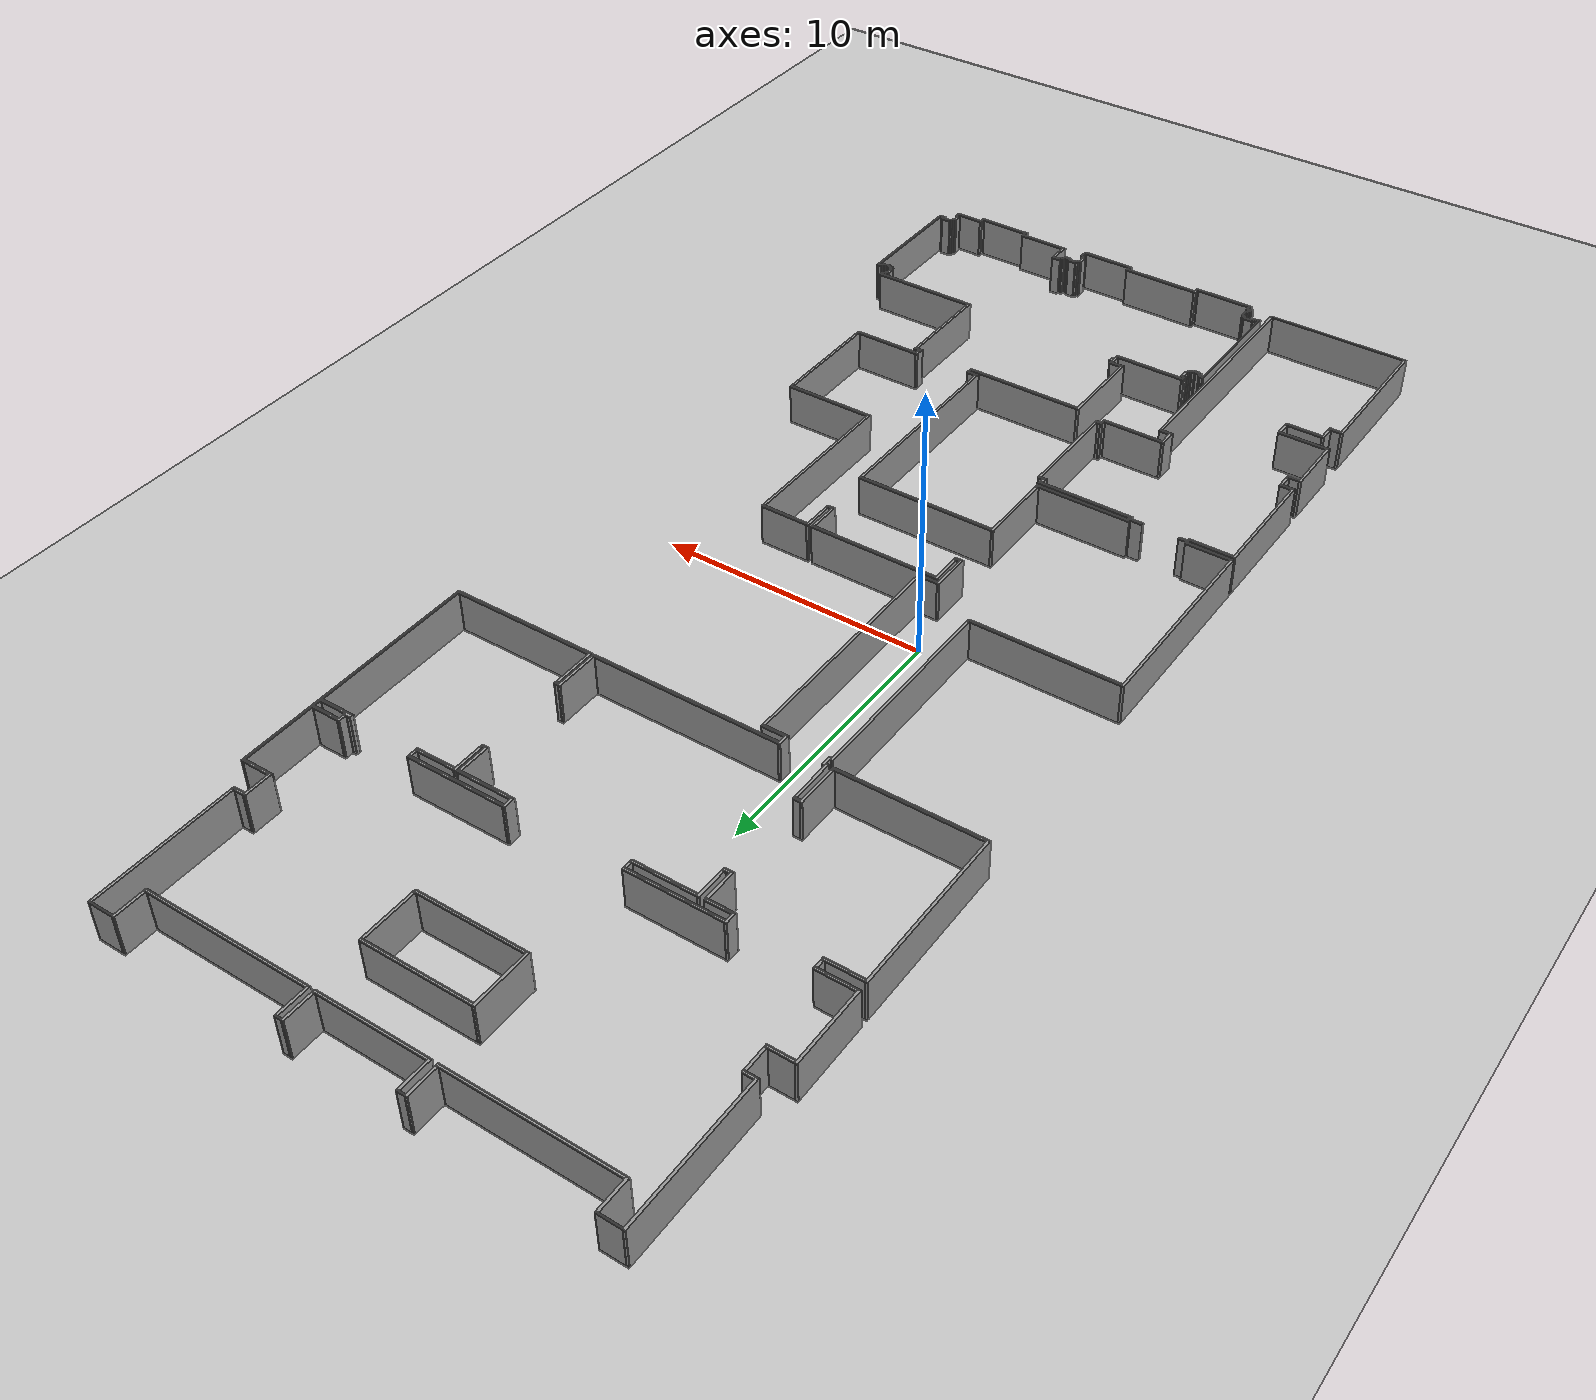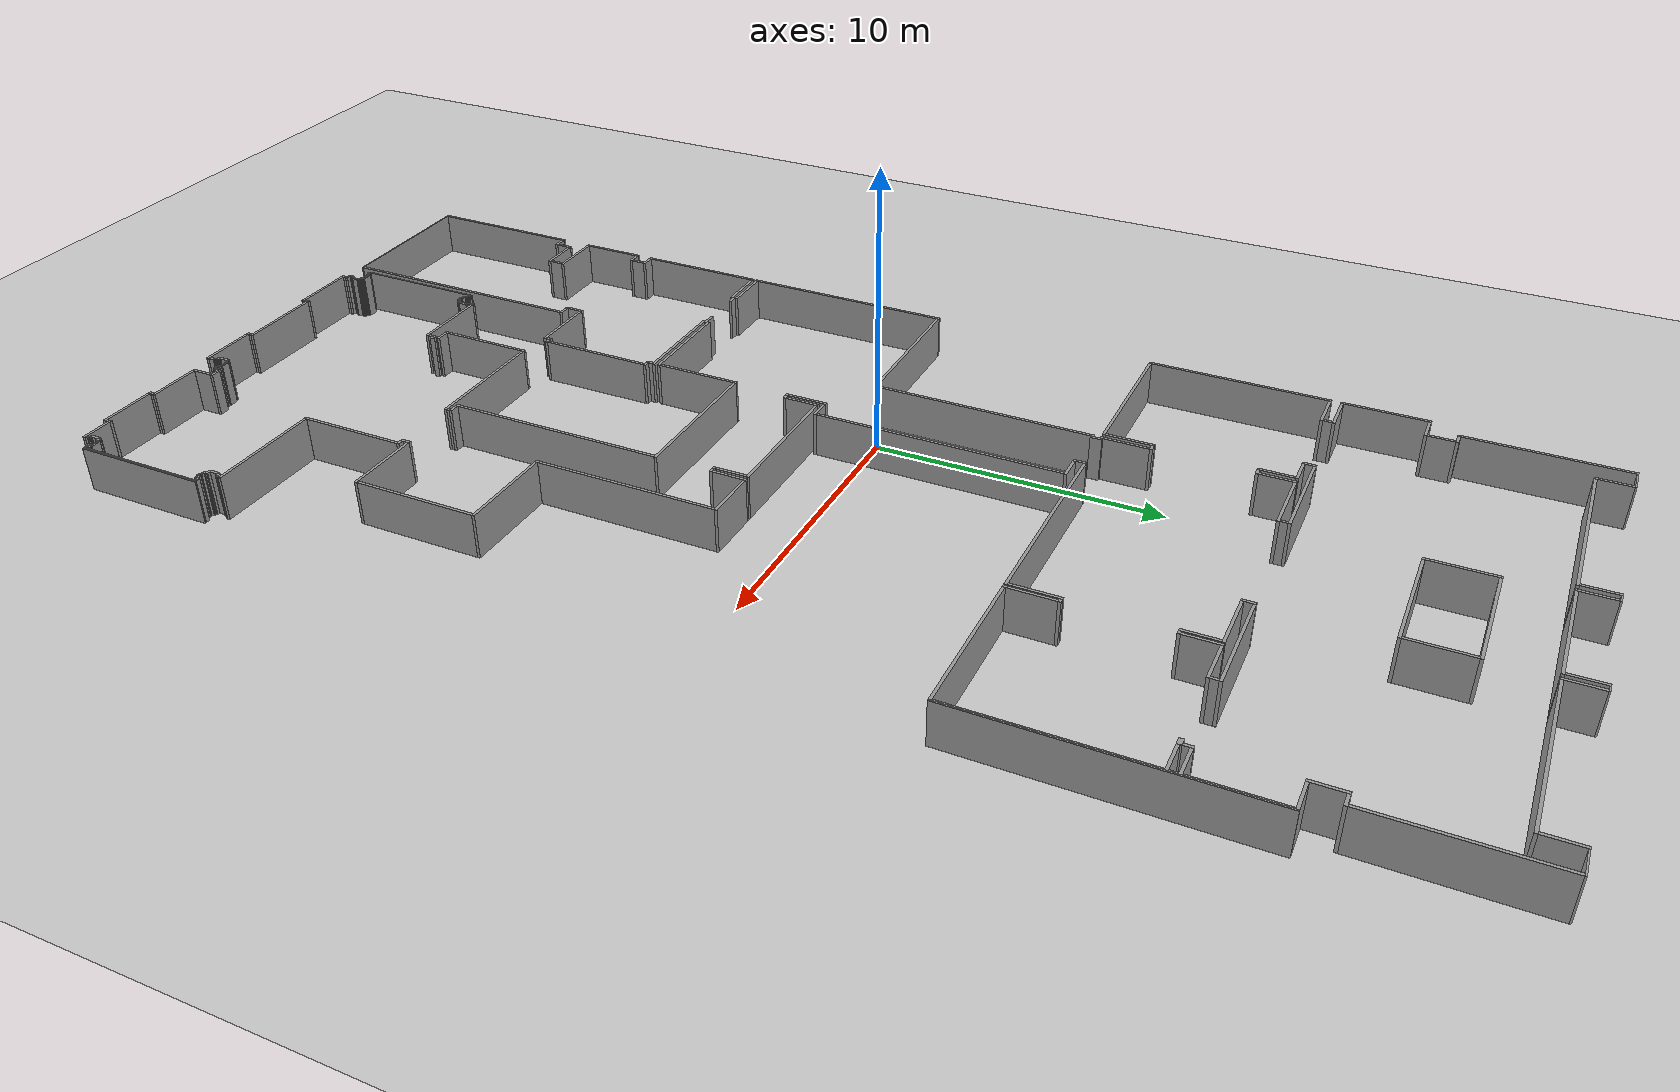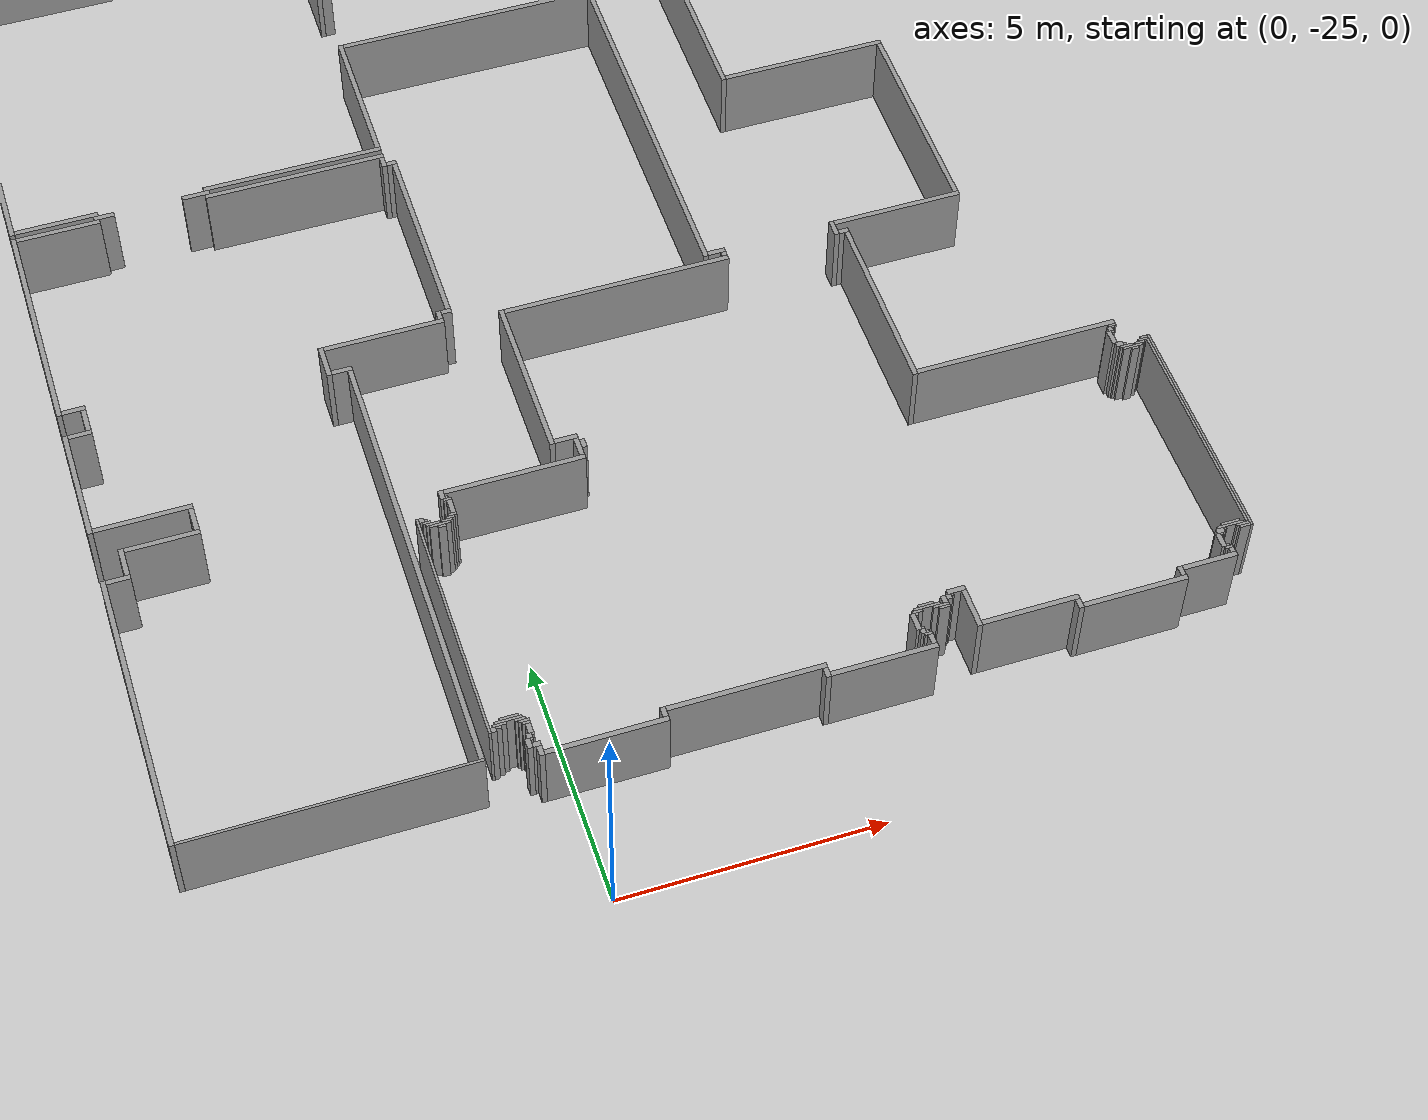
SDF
<sdf version='1.4'>
  <world name='default'>
    <!-- Default physics configuration -->
    <physics type='ode'>
      <gravity>0.000000 0.000000 -9.810000</gravity>
      <ode>
        <solver>
          <type>quick</type>
          <iters>20</iters>
          <sor>1.000000</sor>
        </solver>
        <constraints>
          <cfm>0.000000</cfm>
          <erp>0.200000</erp>
          <contact_max_correcting_vel>100.000000</contact_max_correcting_vel>
          <contact_surface_layer>0.000000</contact_surface_layer>
        </constraints>
      </ode>
      <real_time_update_rate>1000.000000</real_time_update_rate>
      <max_step_size>0.001000</max_step_size>
      <real_time_factor>1.000000</real_time_factor>
      <max_contacts>20</max_contacts>
    </physics>

    <!-- A global light source -->
    <include>
      <uri>model://sun</uri>
    </include>

    <!-- A ground plane -->
    <include>
      <uri>model://ground_plane</uri>
    </include>

    <!-- Walls -->
    <include>
      <uri>model://russian_restaurant</uri>
      <name>walls</name>
      <pose>-7 -22.75 0 0 0 1.5708</pose>
    </include>

    <!-- Camera Position -->
    <gui fullscreen='0'>
      <camera name='user_camera'>
        <pose>5.694260 7.254210 18.725000 0.000000 1.145800 -3.134990</pose>
        <view_controller>orbit</view_controller>
      </camera>
    </gui>
  </world>
</sdf>

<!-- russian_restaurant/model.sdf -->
<sdf version="1.4">
  <model name="RussianRestaurant">
    <static>1</static>
    <link name="Wall_0">
      <collision name="Wall_0_Collision">
        <geometry>
          <box>
            <size>5.70000 0.10000 3.00000</size>
          </box>
        </geometry>
        <pose>3.05000 -0.05000 0 0 0 0.00000</pose>
      </collision>
      <visual name="Wall_0_Visual">
        <geometry>
          <box>
            <size>5.70000 0.10000 3.00000</size>
          </box>
        </geometry>
        <material>
          <script>
            <uri>file://media/materials/scripts/gazebo.material</uri>
            <name>Gazebo/Grey</name>
          </script>
        </material>
        <pose>3.05000 -0.05000 0 0 0 0.00000</pose>
      </visual>
    </link>
    <link name="Wall_1">
      <collision name="Wall_1_Collision">
        <geometry>
          <box>
            <size>2.35000 0.10000 3.00000</size>
          </box>
        </geometry>
        <pose>8.17500 -0.05000 0 0 0 0.00000</pose>
      </collision>
      <visual name="Wall_1_Visual">
        <geometry>
          <box>
            <size>2.35000 0.10000 3.00000</size>
          </box>
        </geometry>
        <material>
          <script>
            <uri>file://media/materials/scripts/gazebo.material</uri>
            <name>Gazebo/Grey</name>
          </script>
        </material>
        <pose>8.17500 -0.05000 0 0 0 0.00000</pose>
      </visual>
    </link>
    <link name="Wall_2">
      <collision name="Wall_2_Collision">
        <geometry>
          <box>
            <size>4.60000 0.10000 3.00000</size>
          </box>
        </geometry>
        <pose>12.15000 -0.05000 0 0 0 0.00000</pose>
      </collision>
      <visual name="Wall_2_Visual">
        <geometry>
          <box>
            <size>4.60000 0.10000 3.00000</size>
          </box>
        </geometry>
        <material>
          <script>
            <uri>file://media/materials/scripts/gazebo.material</uri>
            <name>Gazebo/Grey</name>
          </script>
        </material>
        <pose>12.15000 -0.05000 0 0 0 0.00000</pose>
      </visual>
    </link>
    <link name="Wall_3">
      <collision name="Wall_3_Collision">
        <geometry>
          <box>
            <size>7.55000 0.10000 3.00000</size>
          </box>
        </geometry>
        <pose>18.32500 -0.05000 0 0 0 0.00000</pose>
      </collision>
      <visual name="Wall_3_Visual">
        <geometry>
          <box>
            <size>7.55000 0.10000 3.00000</size>
          </box>
        </geometry>
        <material>
          <script>
            <uri>file://media/materials/scripts/gazebo.material</uri>
            <name>Gazebo/Grey</name>
          </script>
        </material>
        <pose>18.32500 -0.05000 0 0 0 0.00000</pose>
      </visual>
    </link>
    <link name="Wall_4">
      <collision name="Wall_4_Collision">
        <geometry>
          <box>
            <size>6.30000 0.10000 3.00000</size>
          </box>
        </geometry>
        <pose>33.15000 -0.05000 0 0 0 0.00000</pose>
      </collision>
      <visual name="Wall_4_Visual">
        <geometry>
          <box>
            <size>6.30000 0.10000 3.00000</size>
          </box>
        </geometry>
        <material>
          <script>
            <uri>file://media/materials/scripts/gazebo.material</uri>
            <name>Gazebo/Grey</name>
          </script>
        </material>
        <pose>33.15000 -0.05000 0 0 0 0.00000</pose>
      </visual>
    </link>
    <link name="Wall_5">
      <collision name="Wall_5_Collision">
        <geometry>
          <box>
            <size>2.95000 0.10000 3.00000</size>
          </box>
        </geometry>
        <pose>38.07500 -0.05000 0 0 0 0.00000</pose>
      </collision>
      <visual name="Wall_5_Visual">
        <geometry>
          <box>
            <size>2.95000 0.10000 3.00000</size>
          </box>
        </geometry>
        <material>
          <script>
            <uri>file://media/materials/scripts/gazebo.material</uri>
            <name>Gazebo/Grey</name>
          </script>
        </material>
        <pose>38.07500 -0.05000 0 0 0 0.00000</pose>
      </visual>
    </link>
    <link name="Wall_6">
      <collision name="Wall_6_Collision">
        <geometry>
          <box>
            <size>0.05000 5.40000 3.00000</size>
          </box>
        </geometry>
        <pose>0.22500 -2.80000 0 0 0 0.00000</pose>
      </collision>
      <visual name="Wall_6_Visual">
        <geometry>
          <box>
            <size>0.05000 5.40000 3.00000</size>
          </box>
        </geometry>
        <material>
          <script>
            <uri>file://media/materials/scripts/gazebo.material</uri>
            <name>Gazebo/Grey</name>
          </script>
        </material>
        <pose>0.22500 -2.80000 0 0 0 0.00000</pose>
      </visual>
    </link>
    <link name="Wall_7">
      <collision name="Wall_7_Collision">
        <geometry>
          <box>
            <size>0.10000 0.45000 3.00000</size>
          </box>
        </geometry>
        <pose>5.85000 -0.32500 0 0 0 0.00000</pose>
      </collision>
      <visual name="Wall_7_Visual">
        <geometry>
          <box>
            <size>0.10000 0.45000 3.00000</size>
          </box>
        </geometry>
        <material>
          <script>
            <uri>file://media/materials/scripts/gazebo.material</uri>
            <name>Gazebo/Grey</name>
          </script>
        </material>
        <pose>5.85000 -0.32500 0 0 0 0.00000</pose>
      </visual>
    </link>
    <link name="Wall_8">
      <collision name="Wall_8_Collision">
        <geometry>
          <box>
            <size>0.10000 1.85000 3.00000</size>
          </box>
        </geometry>
        <pose>7.05000 -1.02500 0 0 0 0.00000</pose>
      </collision>
      <visual name="Wall_8_Visual">
        <geometry>
          <box>
            <size>0.10000 1.85000 3.00000</size>
          </box>
        </geometry>
        <material>
          <script>
            <uri>file://media/materials/scripts/gazebo.material</uri>
            <name>Gazebo/Grey</name>
          </script>
        </material>
        <pose>7.05000 -1.02500 0 0 0 0.00000</pose>
      </visual>
    </link>
    <link name="Wall_9">
      <collision name="Wall_9_Collision">
        <geometry>
          <box>
            <size>0.10000 0.45000 3.00000</size>
          </box>
        </geometry>
        <pose>9.30000 -0.32500 0 0 0 0.00000</pose>
      </collision>
      <visual name="Wall_9_Visual">
        <geometry>
          <box>
            <size>0.10000 0.45000 3.00000</size>
          </box>
        </geometry>
        <material>
          <script>
            <uri>file://media/materials/scripts/gazebo.material</uri>
            <name>Gazebo/Grey</name>
          </script>
        </material>
        <pose>9.30000 -0.32500 0 0 0 0.00000</pose>
      </visual>
    </link>
    <link name="Wall_10">
      <collision name="Wall_10_Collision">
        <geometry>
          <box>
            <size>0.10000 0.45000 3.00000</size>
          </box>
        </geometry>
        <pose>9.90000 -0.32500 0 0 0 0.00000</pose>
      </collision>
      <visual name="Wall_10_Visual">
        <geometry>
          <box>
            <size>0.10000 0.45000 3.00000</size>
          </box>
        </geometry>
        <material>
          <script>
            <uri>file://media/materials/scripts/gazebo.material</uri>
            <name>Gazebo/Grey</name>
          </script>
        </material>
        <pose>9.90000 -0.32500 0 0 0 0.00000</pose>
      </visual>
    </link>
    <link name="Wall_11">
      <collision name="Wall_11_Collision">
        <geometry>
          <box>
            <size>0.10000 1.65000 3.00000</size>
          </box>
        </geometry>
        <pose>14.40000 -0.92500 0 0 0 0.00000</pose>
      </collision>
      <visual name="Wall_11_Visual">
        <geometry>
          <box>
            <size>0.10000 1.65000 3.00000</size>
          </box>
        </geometry>
        <material>
          <script>
            <uri>file://media/materials/scripts/gazebo.material</uri>
            <name>Gazebo/Grey</name>
          </script>
        </material>
        <pose>14.40000 -0.92500 0 0 0 0.00000</pose>
      </visual>
    </link>
    <link name="Wall_12">
      <collision name="Wall_12_Collision">
        <geometry>
          <box>
            <size>0.10000 1.65000 3.00000</size>
          </box>
        </geometry>
        <pose>14.60000 -0.92500 0 0 0 0.00000</pose>
      </collision>
      <visual name="Wall_12_Visual">
        <geometry>
          <box>
            <size>0.10000 1.65000 3.00000</size>
          </box>
        </geometry>
        <material>
          <script>
            <uri>file://media/materials/scripts/gazebo.material</uri>
            <name>Gazebo/Grey</name>
          </script>
        </material>
        <pose>14.60000 -0.92500 0 0 0 0.00000</pose>
      </visual>
    </link>
    <link name="Wall_13">
      <collision name="Wall_13_Collision">
        <geometry>
          <box>
            <size>0.10000 5.55000 3.00000</size>
          </box>
        </geometry>
        <pose>22.05000 -2.87500 0 0 0 0.00000</pose>
      </collision>
      <visual name="Wall_13_Visual">
        <geometry>
          <box>
            <size>0.10000 5.55000 3.00000</size>
          </box>
        </geometry>
        <material>
          <script>
            <uri>file://media/materials/scripts/gazebo.material</uri>
            <name>Gazebo/Grey</name>
          </script>
        </material>
        <pose>22.05000 -2.87500 0 0 0 0.00000</pose>
      </visual>
    </link>
    <link name="Wall_14">
      <collision name="Wall_14_Collision">
        <geometry>
          <box>
            <size>0.10000 5.30000 3.00000</size>
          </box>
        </geometry>
        <pose>30.05000 -2.75000 0 0 0 0.00000</pose>
      </collision>
      <visual name="Wall_14_Visual">
        <geometry>
          <box>
            <size>0.10000 5.30000 3.00000</size>
          </box>
        </geometry>
        <material>
          <script>
            <uri>file://media/materials/scripts/gazebo.material</uri>
            <name>Gazebo/Grey</name>
          </script>
        </material>
        <pose>30.05000 -2.75000 0 0 0 0.00000</pose>
      </visual>
    </link>
    <link name="Wall_15">
      <collision name="Wall_15_Collision">
        <geometry>
          <box>
            <size>0.10000 1.40000 3.00000</size>
          </box>
        </geometry>
        <pose>36.25000 -0.80000 0 0 0 0.00000</pose>
      </collision>
      <visual name="Wall_15_Visual">
        <geometry>
          <box>
            <size>0.10000 1.40000 3.00000</size>
          </box>
        </geometry>
        <material>
          <script>
            <uri>file://media/materials/scripts/gazebo.material</uri>
            <name>Gazebo/Grey</name>
          </script>
        </material>
        <pose>36.25000 -0.80000 0 0 0 0.00000</pose>
      </visual>
    </link>
    <link name="Wall_16">
      <collision name="Wall_16_Collision">
        <geometry>
          <box>
            <size>0.10000 1.40000 3.00000</size>
          </box>
        </geometry>
        <pose>36.65000 -0.80000 0 0 0 0.00000</pose>
      </collision>
      <visual name="Wall_16_Visual">
        <geometry>
          <box>
            <size>0.10000 1.40000 3.00000</size>
          </box>
        </geometry>
        <material>
          <script>
            <uri>file://media/materials/scripts/gazebo.material</uri>
            <name>Gazebo/Grey</name>
          </script>
        </material>
        <pose>36.65000 -0.80000 0 0 0 0.00000</pose>
      </visual>
    </link>
    <link name="Wall_17">
      <collision name="Wall_17_Collision">
        <geometry>
          <box>
            <size>0.10000 0.95000 3.00000</size>
          </box>
        </geometry>
        <pose>39.50000 -0.57500 0 0 0 0.00000</pose>
      </collision>
      <visual name="Wall_17_Visual">
        <geometry>
          <box>
            <size>0.10000 0.95000 3.00000</size>
          </box>
        </geometry>
        <material>
          <script>
            <uri>file://media/materials/scripts/gazebo.material</uri>
            <name>Gazebo/Grey</name>
          </script>
        </material>
        <pose>39.50000 -0.57500 0 0 0 0.00000</pose>
      </visual>
    </link>
    <link name="Wall_18">
      <collision name="Wall_18_Collision">
        <geometry>
          <box>
            <size>0.60000 0.10000 3.00000</size>
          </box>
        </geometry>
        <pose>6.20000 -0.50000 0 0 0 0.00000</pose>
      </collision>
      <visual name="Wall_18_Visual">
        <geometry>
          <box>
            <size>0.60000 0.10000 3.00000</size>
          </box>
        </geometry>
        <material>
          <script>
            <uri>file://media/materials/scripts/gazebo.material</uri>
            <name>Gazebo/Grey</name>
          </script>
        </material>
        <pose>6.20000 -0.50000 0 0 0 0.00000</pose>
      </visual>
    </link>
    <link name="Wall_19">
      <collision name="Wall_19_Collision">
        <geometry>
          <box>
            <size>0.50000 0.10000 3.00000</size>
          </box>
        </geometry>
        <pose>9.60000 -0.50000 0 0 0 0.00000</pose>
      </collision>
      <visual name="Wall_19_Visual">
        <geometry>
          <box>
            <size>0.50000 0.10000 3.00000</size>
          </box>
        </geometry>
        <material>
          <script>
            <uri>file://media/materials/scripts/gazebo.material</uri>
            <name>Gazebo/Grey</name>
          </script>
        </material>
        <pose>9.60000 -0.50000 0 0 0 0.00000</pose>
      </visual>
    </link>
    <link name="Wall_20">
      <collision name="Wall_20_Collision">
        <geometry>
          <box>
            <size>0.10000 1.40000 3.00000</size>
          </box>
        </geometry>
        <pose>6.45000 -1.25000 0 0 0 0.00000</pose>
      </collision>
      <visual name="Wall_20_Visual">
        <geometry>
          <box>
            <size>0.10000 1.40000 3.00000</size>
          </box>
        </geometry>
        <material>
          <script>
            <uri>file://media/materials/scripts/gazebo.material</uri>
            <name>Gazebo/Grey</name>
          </script>
        </material>
        <pose>6.45000 -1.25000 0 0 0 0.00000</pose>
      </visual>
    </link>
    <link name="Wall_21">
      <collision name="Wall_21_Collision">
        <geometry>
          <box>
            <size>5.45000 0.10000 3.00000</size>
          </box>
        </geometry>
        <pose>43.17500 -0.60000 0 0 0 0.00000</pose>
      </collision>
      <visual name="Wall_21_Visual">
        <geometry>
          <box>
            <size>5.45000 0.10000 3.00000</size>
          </box>
        </geometry>
        <material>
          <script>
            <uri>file://media/materials/scripts/gazebo.material</uri>
            <name>Gazebo/Grey</name>
          </script>
        </material>
        <pose>43.17500 -0.60000 0 0 0 0.00000</pose>
      </visual>
    </link>
    <link name="Wall_22">
      <collision name="Wall_22_Collision">
        <geometry>
          <box>
            <size>0.10000 0.40000 3.00000</size>
          </box>
        </geometry>
        <pose>40.50000 -0.85000 0 0 0 0.00000</pose>
      </collision>
      <visual name="Wall_22_Visual">
        <geometry>
          <box>
            <size>0.10000 0.40000 3.00000</size>
          </box>
        </geometry>
        <material>
          <script>
            <uri>file://media/materials/scripts/gazebo.material</uri>
            <name>Gazebo/Grey</name>
          </script>
        </material>
        <pose>40.50000 -0.85000 0 0 0 0.00000</pose>
      </visual>
    </link>
    <link name="Wall_23">
      <collision name="Wall_23_Collision">
        <geometry>
          <box>
            <size>0.05000 0.85000 3.00000</size>
          </box>
        </geometry>
        <pose>45.87500 -1.07500 0 0 0 0.00000</pose>
      </collision>
      <visual name="Wall_23_Visual">
        <geometry>
          <box>
            <size>0.05000 0.85000 3.00000</size>
          </box>
        </geometry>
        <material>
          <script>
            <uri>file://media/materials/scripts/gazebo.material</uri>
            <name>Gazebo/Grey</name>
          </script>
        </material>
        <pose>45.87500 -1.07500 0 0 0 0.00000</pose>
      </visual>
    </link>
    <link name="Wall_24">
      <collision name="Wall_24_Collision">
        <geometry>
          <box>
            <size>0.90000 0.10000 3.00000</size>
          </box>
        </geometry>
        <pose>40.00000 -1.00000 0 0 0 0.00000</pose>
      </collision>
      <visual name="Wall_24_Visual">
        <geometry>
          <box>
            <size>0.90000 0.10000 3.00000</size>
          </box>
        </geometry>
        <material>
          <script>
            <uri>file://media/materials/scripts/gazebo.material</uri>
            <name>Gazebo/Grey</name>
          </script>
        </material>
        <pose>40.00000 -1.00000 0 0 0 0.00000</pose>
      </visual>
    </link>
    <link name="Wall_25">
      <collision name="Wall_25_Collision">
        <geometry>
          <box>
            <size>0.30000 0.10000 3.00000</size>
          </box>
        </geometry>
        <pose>36.45000 -1.45000 0 0 0 0.00000</pose>
      </collision>
      <visual name="Wall_25_Visual">
        <geometry>
          <box>
            <size>0.30000 0.10000 3.00000</size>
          </box>
        </geometry>
        <material>
          <script>
            <uri>file://media/materials/scripts/gazebo.material</uri>
            <name>Gazebo/Grey</name>
          </script>
        </material>
        <pose>36.45000 -1.45000 0 0 0 0.00000</pose>
      </visual>
    </link>
    <link name="Wall_26">
      <collision name="Wall_26_Collision">
        <geometry>
          <box>
            <size>1.20000 0.10000 3.00000</size>
          </box>
        </geometry>
        <pose>45.25000 -1.45000 0 0 0 0.00000</pose>
      </collision>
      <visual name="Wall_26_Visual">
        <geometry>
          <box>
            <size>1.20000 0.10000 3.00000</size>
          </box>
        </geometry>
        <material>
          <script>
            <uri>file://media/materials/scripts/gazebo.material</uri>
            <name>Gazebo/Grey</name>
          </script>
        </material>
        <pose>45.25000 -1.45000 0 0 0 0.00000</pose>
      </visual>
    </link>
    <link name="Wall_27">
      <collision name="Wall_27_Collision">
        <geometry>
          <box>
            <size>0.10000 6.15000 3.00000</size>
          </box>
        </geometry>
        <pose>44.70000 -4.57500 0 0 0 0.00000</pose>
      </collision>
      <visual name="Wall_27_Visual">
        <geometry>
          <box>
            <size>0.10000 6.15000 3.00000</size>
          </box>
        </geometry>
        <material>
          <script>
            <uri>file://media/materials/scripts/gazebo.material</uri>
            <name>Gazebo/Grey</name>
          </script>
        </material>
        <pose>44.70000 -4.57500 0 0 0 0.00000</pose>
      </visual>
    </link>
    <link name="Wall_28">
      <collision name="Wall_28_Collision">
        <geometry>
          <box>
            <size>0.10000 0.40000 3.00000</size>
          </box>
        </geometry>
        <pose>14.50000 -1.85000 0 0 0 0.00000</pose>
      </collision>
      <visual name="Wall_28_Visual">
        <geometry>
          <box>
            <size>0.10000 0.40000 3.00000</size>
          </box>
        </geometry>
        <material>
          <script>
            <uri>file://media/materials/scripts/gazebo.material</uri>
            <name>Gazebo/Grey</name>
          </script>
        </material>
        <pose>14.50000 -1.85000 0 0 0 0.00000</pose>
      </visual>
    </link>
    <link name="Wall_29">
      <collision name="Wall_29_Collision">
        <geometry>
          <box>
            <size>0.50000 0.10000 3.00000</size>
          </box>
        </geometry>
        <pose>6.75000 -1.90000 0 0 0 0.00000</pose>
      </collision>
      <visual name="Wall_29_Visual">
        <geometry>
          <box>
            <size>0.50000 0.10000 3.00000</size>
          </box>
        </geometry>
        <material>
          <script>
            <uri>file://media/materials/scripts/gazebo.material</uri>
            <name>Gazebo/Grey</name>
          </script>
        </material>
        <pose>6.75000 -1.90000 0 0 0 0.00000</pose>
      </visual>
    </link>
    <link name="Wall_30">
      <collision name="Wall_30_Collision">
        <geometry>
          <box>
            <size>0.10000 0.55000 3.00000</size>
          </box>
        </geometry>
        <pose>14.50000 -3.67500 0 0 0 0.00000</pose>
      </collision>
      <visual name="Wall_30_Visual">
        <geometry>
          <box>
            <size>0.10000 0.55000 3.00000</size>
          </box>
        </geometry>
        <material>
          <script>
            <uri>file://media/materials/scripts/gazebo.material</uri>
            <name>Gazebo/Grey</name>
          </script>
        </material>
        <pose>14.50000 -3.67500 0 0 0 0.00000</pose>
      </visual>
    </link>
    <link name="Wall_31">
      <collision name="Wall_31_Collision">
        <geometry>
          <box>
            <size>0.10000 3.60000 3.00000</size>
          </box>
        </geometry>
        <pose>14.40000 -5.65000 0 0 0 0.00000</pose>
      </collision>
      <visual name="Wall_31_Visual">
        <geometry>
          <box>
            <size>0.10000 3.60000 3.00000</size>
          </box>
        </geometry>
        <material>
          <script>
            <uri>file://media/materials/scripts/gazebo.material</uri>
            <name>Gazebo/Grey</name>
          </script>
        </material>
        <pose>14.40000 -5.65000 0 0 0 0.00000</pose>
      </visual>
    </link>
    <link name="Wall_32">
      <collision name="Wall_32_Collision">
        <geometry>
          <box>
            <size>0.10000 3.60000 3.00000</size>
          </box>
        </geometry>
        <pose>14.60000 -5.65000 0 0 0 0.00000</pose>
      </collision>
      <visual name="Wall_32_Visual">
        <geometry>
          <box>
            <size>0.10000 3.60000 3.00000</size>
          </box>
        </geometry>
        <material>
          <script>
            <uri>file://media/materials/scripts/gazebo.material</uri>
            <name>Gazebo/Grey</name>
          </script>
        </material>
        <pose>14.60000 -5.65000 0 0 0 0.00000</pose>
      </visual>
    </link>
    <link name="Wall_33">
      <collision name="Wall_33_Collision">
        <geometry>
          <box>
            <size>0.45000 0.10000 3.00000</size>
          </box>
        </geometry>
        <pose>36.47500 -4.40000 0 0 0 0.00000</pose>
      </collision>
      <visual name="Wall_33_Visual">
        <geometry>
          <box>
            <size>0.45000 0.10000 3.00000</size>
          </box>
        </geometry>
        <material>
          <script>
            <uri>file://media/materials/scripts/gazebo.material</uri>
            <name>Gazebo/Grey</name>
          </script>
        </material>
        <pose>36.47500 -4.40000 0 0 0 0.00000</pose>
      </visual>
    </link>
    <link name="Wall_34">
      <collision name="Wall_34_Collision">
        <geometry>
          <box>
            <size>0.10000 0.95000 3.00000</size>
          </box>
        </geometry>
        <pose>36.30000 -4.92500 0 0 0 0.00000</pose>
      </collision>
      <visual name="Wall_34_Visual">
        <geometry>
          <box>
            <size>0.10000 0.95000 3.00000</size>
          </box>
        </geometry>
        <material>
          <script>
            <uri>file://media/materials/scripts/gazebo.material</uri>
            <name>Gazebo/Grey</name>
          </script>
        </material>
        <pose>36.30000 -4.92500 0 0 0 0.00000</pose>
      </visual>
    </link>
    <link name="Wall_35">
      <collision name="Wall_35_Collision">
        <geometry>
          <box>
            <size>0.10000 3.55000 3.00000</size>
          </box>
        </geometry>
        <pose>36.65000 -6.22500 0 0 0 0.00000</pose>
      </collision>
      <visual name="Wall_35_Visual">
        <geometry>
          <box>
            <size>0.10000 3.55000 3.00000</size>
          </box>
        </geometry>
        <material>
          <script>
            <uri>file://media/materials/scripts/gazebo.material</uri>
            <name>Gazebo/Grey</name>
          </script>
        </material>
        <pose>36.65000 -6.22500 0 0 0 0.00000</pose>
      </visual>
    </link>
    <link name="Wall_36">
      <collision name="Wall_36_Collision">
        <geometry>
          <box>
            <size>0.70000 0.10000 3.00000</size>
          </box>
        </geometry>
        <pose>9.60000 -5.05000 0 0 0 0.00000</pose>
      </collision>
      <visual name="Wall_36_Visual">
        <geometry>
          <box>
            <size>0.70000 0.10000 3.00000</size>
          </box>
        </geometry>
        <material>
          <script>
            <uri>file://media/materials/scripts/gazebo.material</uri>
            <name>Gazebo/Grey</name>
          </script>
        </material>
        <pose>9.60000 -5.05000 0 0 0 0.00000</pose>
      </visual>
    </link>
    <link name="Wall_37">
      <collision name="Wall_37_Collision">
        <geometry>
          <box>
            <size>0.10000 0.40000 3.00000</size>
          </box>
        </geometry>
        <pose>9.30000 -5.30000 0 0 0 0.00000</pose>
      </collision>
      <visual name="Wall_37_Visual">
        <geometry>
          <box>
            <size>0.10000 0.40000 3.00000</size>
          </box>
        </geometry>
        <material>
          <script>
            <uri>file://media/materials/scripts/gazebo.material</uri>
            <name>Gazebo/Grey</name>
          </script>
        </material>
        <pose>9.30000 -5.30000 0 0 0 0.00000</pose>
      </visual>
    </link>
    <link name="Wall_38">
      <collision name="Wall_38_Collision">
        <geometry>
          <box>
            <size>0.10000 2.35000 3.00000</size>
          </box>
        </geometry>
        <pose>9.90000 -6.27500 0 0 0 0.00000</pose>
      </collision>
      <visual name="Wall_38_Visual">
        <geometry>
          <box>
            <size>0.10000 2.35000 3.00000</size>
          </box>
        </geometry>
        <material>
          <script>
            <uri>file://media/materials/scripts/gazebo.material</uri>
            <name>Gazebo/Grey</name>
          </script>
        </material>
        <pose>9.90000 -6.27500 0 0 0 0.00000</pose>
      </visual>
    </link>
    <link name="Wall_39">
      <collision name="Wall_39_Collision">
        <geometry>
          <box>
            <size>1.65000 0.10000 3.00000</size>
          </box>
        </geometry>
        <pose>30.92500 -5.35000 0 0 0 0.00000</pose>
      </collision>
      <visual name="Wall_39_Visual">
        <geometry>
          <box>
            <size>1.65000 0.10000 3.00000</size>
          </box>
        </geometry>
        <material>
          <script>
            <uri>file://media/materials/scripts/gazebo.material</uri>
            <name>Gazebo/Grey</name>
          </script>
        </material>
        <pose>30.92500 -5.35000 0 0 0 0.00000</pose>
      </visual>
    </link>
    <link name="Wall_40">
      <collision name="Wall_40_Collision">
        <geometry>
          <box>
            <size>1.20000 0.10000 3.00000</size>
          </box>
        </geometry>
        <pose>35.65000 -5.35000 0 0 0 0.00000</pose>
      </collision>
      <visual name="Wall_40_Visual">
        <geometry>
          <box>
            <size>1.20000 0.10000 3.00000</size>
          </box>
        </geometry>
        <material>
          <script>
            <uri>file://media/materials/scripts/gazebo.material</uri>
            <name>Gazebo/Grey</name>
          </script>
        </material>
        <pose>35.65000 -5.35000 0 0 0 0.00000</pose>
      </visual>
    </link>
    <link name="Wall_41">
      <collision name="Wall_41_Collision">
        <geometry>
          <box>
            <size>9.00000 0.10000 3.00000</size>
          </box>
        </geometry>
        <pose>4.75000 -5.45000 0 0 0 0.00000</pose>
      </collision>
      <visual name="Wall_41_Visual">
        <geometry>
          <box>
            <size>9.00000 0.10000 3.00000</size>
          </box>
        </geometry>
        <material>
          <script>
            <uri>file://media/materials/scripts/gazebo.material</uri>
            <name>Gazebo/Grey</name>
          </script>
        </material>
        <pose>4.75000 -5.45000 0 0 0 0.00000</pose>
      </visual>
    </link>
    <link name="Wall_42">
      <collision name="Wall_42_Collision">
        <geometry>
          <box>
            <size>0.10000 0.25000 3.00000</size>
          </box>
        </geometry>
        <pose>31.70000 -5.52500 0 0 0 0.00000</pose>
      </collision>
      <visual name="Wall_42_Visual">
        <geometry>
          <box>
            <size>0.10000 0.25000 3.00000</size>
          </box>
        </geometry>
        <material>
          <script>
            <uri>file://media/materials/scripts/gazebo.material</uri>
            <name>Gazebo/Grey</name>
          </script>
        </material>
        <pose>31.70000 -5.52500 0 0 0 0.00000</pose>
      </visual>
    </link>
    <link name="Wall_43">
      <collision name="Wall_43_Collision">
        <geometry>
          <box>
            <size>0.10000 0.25000 3.00000</size>
          </box>
        </geometry>
        <pose>35.10000 -5.52500 0 0 0 0.00000</pose>
      </collision>
      <visual name="Wall_43_Visual">
        <geometry>
          <box>
            <size>0.10000 0.25000 3.00000</size>
          </box>
        </geometry>
        <material>
          <script>
            <uri>file://media/materials/scripts/gazebo.material</uri>
            <name>Gazebo/Grey</name>
          </script>
        </material>
        <pose>35.10000 -5.52500 0 0 0 0.00000</pose>
      </visual>
    </link>
    <link name="Wall_44">
      <collision name="Wall_44_Collision">
        <geometry>
          <box>
            <size>7.70000 0.10000 3.00000</size>
          </box>
        </geometry>
        <pose>25.95000 -5.60000 0 0 0 0.00000</pose>
      </collision>
      <visual name="Wall_44_Visual">
        <geometry>
          <box>
            <size>7.70000 0.10000 3.00000</size>
          </box>
        </geometry>
        <material>
          <script>
            <uri>file://media/materials/scripts/gazebo.material</uri>
            <name>Gazebo/Grey</name>
          </script>
        </material>
        <pose>25.95000 -5.60000 0 0 0 0.00000</pose>
      </visual>
    </link>
    <link name="Wall_45">
      <collision name="Wall_45_Collision">
        <geometry>
          <box>
            <size>1.65000 0.10000 3.00000</size>
          </box>
        </geometry>
        <pose>30.82500 -5.60000 0 0 0 0.00000</pose>
      </collision>
      <visual name="Wall_45_Visual">
        <geometry>
          <box>
            <size>1.65000 0.10000 3.00000</size>
          </box>
        </geometry>
        <material>
          <script>
            <uri>file://media/materials/scripts/gazebo.material</uri>
            <name>Gazebo/Grey</name>
          </script>
        </material>
        <pose>30.82500 -5.60000 0 0 0 0.00000</pose>
      </visual>
    </link>
    <link name="Wall_46">
      <collision name="Wall_46_Collision">
        <geometry>
          <box>
            <size>1.20000 0.10000 3.00000</size>
          </box>
        </geometry>
        <pose>35.75000 -5.60000 0 0 0 0.00000</pose>
      </collision>
      <visual name="Wall_46_Visual">
        <geometry>
          <box>
            <size>1.20000 0.10000 3.00000</size>
          </box>
        </geometry>
        <material>
          <script>
            <uri>file://media/materials/scripts/gazebo.material</uri>
            <name>Gazebo/Grey</name>
          </script>
        </material>
        <pose>35.75000 -5.60000 0 0 0 0.00000</pose>
      </visual>
    </link>
    <link name="Wall_47">
      <collision name="Wall_47_Collision">
        <geometry>
          <box>
            <size>0.40000 0.10000 3.00000</size>
          </box>
        </geometry>
        <pose>29.90000 -5.70000 0 0 0 0.00000</pose>
      </collision>
      <visual name="Wall_47_Visual">
        <geometry>
          <box>
            <size>0.40000 0.10000 3.00000</size>
          </box>
        </geometry>
        <material>
          <script>
            <uri>file://media/materials/scripts/gazebo.material</uri>
            <name>Gazebo/Grey</name>
          </script>
        </material>
        <pose>29.90000 -5.70000 0 0 0 0.00000</pose>
      </visual>
    </link>
    <link name="Wall_48">
      <collision name="Wall_48_Collision">
        <geometry>
          <box>
            <size>0.10000 2.35000 3.00000</size>
          </box>
        </geometry>
        <pose>36.30000 -6.82500 0 0 0 0.00000</pose>
      </collision>
      <visual name="Wall_48_Visual">
        <geometry>
          <box>
            <size>0.10000 2.35000 3.00000</size>
          </box>
        </geometry>
        <material>
          <script>
            <uri>file://media/materials/scripts/gazebo.material</uri>
            <name>Gazebo/Grey</name>
          </script>
        </material>
        <pose>36.30000 -6.82500 0 0 0 0.00000</pose>
      </visual>
    </link>
    <link name="Wall_49">
      <collision name="Wall_49_Collision">
        <geometry>
          <box>
            <size>4.80000 0.05000 3.00000</size>
          </box>
        </geometry>
        <pose>3.10000 -5.72500 0 0 0 0.00000</pose>
      </collision>
      <visual name="Wall_49_Visual">
        <geometry>
          <box>
            <size>4.80000 0.05000 3.00000</size>
          </box>
        </geometry>
        <material>
          <script>
            <uri>file://media/materials/scripts/gazebo.material</uri>
            <name>Gazebo/Grey</name>
          </script>
        </material>
        <pose>3.10000 -5.72500 0 0 0 0.00000</pose>
      </visual>
    </link>
    <link name="Wall_50">
      <collision name="Wall_50_Collision">
        <geometry>
          <box>
            <size>0.10000 0.10000 3.00000</size>
          </box>
        </geometry>
        <pose>0.75000 -5.80000 0 0 0 0.00000</pose>
      </collision>
      <visual name="Wall_50_Visual">
        <geometry>
          <box>
            <size>0.10000 0.10000 3.00000</size>
          </box>
        </geometry>
        <material>
          <script>
            <uri>file://media/materials/scripts/gazebo.material</uri>
            <name>Gazebo/Grey</name>
          </script>
        </material>
        <pose>0.75000 -5.80000 0 0 0 0.00000</pose>
      </visual>
    </link>
    <link name="Wall_51">
      <collision name="Wall_51_Collision">
        <geometry>
          <box>
            <size>0.10000 0.10000 3.00000</size>
          </box>
        </geometry>
        <pose>5.45000 -5.80000 0 0 0 0.00000</pose>
      </collision>
      <visual name="Wall_51_Visual">
        <geometry>
          <box>
            <size>0.10000 0.10000 3.00000</size>
          </box>
        </geometry>
        <material>
          <script>
            <uri>file://media/materials/scripts/gazebo.material</uri>
            <name>Gazebo/Grey</name>
          </script>
        </material>
        <pose>5.45000 -5.80000 0 0 0 0.00000</pose>
      </visual>
    </link>
    <link name="Wall_52">
      <collision name="Wall_52_Collision">
        <geometry>
          <box>
            <size>0.05000 0.25000 3.00000</size>
          </box>
        </geometry>
        <pose>0.82500 -5.92500 0 0 0 0.00000</pose>
      </collision>
      <visual name="Wall_52_Visual">
        <geometry>
          <box>
            <size>0.05000 0.25000 3.00000</size>
          </box>
        </geometry>
        <material>
          <script>
            <uri>file://media/materials/scripts/gazebo.material</uri>
            <name>Gazebo/Grey</name>
          </script>
        </material>
        <pose>0.82500 -5.92500 0 0 0 0.00000</pose>
      </visual>
    </link>
    <link name="Wall_53">
      <collision name="Wall_53_Collision">
        <geometry>
          <box>
            <size>0.05000 0.15000 3.00000</size>
          </box>
        </geometry>
        <pose>5.37500 -5.87500 0 0 0 0.00000</pose>
      </collision>
      <visual name="Wall_53_Visual">
        <geometry>
          <box>
            <size>0.05000 0.15000 3.00000</size>
          </box>
        </geometry>
        <material>
          <script>
            <uri>file://media/materials/scripts/gazebo.material</uri>
            <name>Gazebo/Grey</name>
          </script>
        </material>
        <pose>5.37500 -5.87500 0 0 0 0.00000</pose>
      </visual>
    </link>
    <link name="Wall_54">
      <collision name="Wall_54_Collision">
        <geometry>
          <box>
            <size>0.05000 0.10000 3.00000</size>
          </box>
        </geometry>
        <pose>0.77500 -5.90000 0 0 0 0.00000</pose>
      </collision>
      <visual name="Wall_54_Visual">
        <geometry>
          <box>
            <size>0.05000 0.10000 3.00000</size>
          </box>
        </geometry>
        <material>
          <script>
            <uri>file://media/materials/scripts/gazebo.material</uri>
            <name>Gazebo/Grey</name>
          </script>
        </material>
        <pose>0.77500 -5.90000 0 0 0 0.00000</pose>
      </visual>
    </link>
    <link name="Wall_55">
      <collision name="Wall_55_Collision">
        <geometry>
          <box>
            <size>0.05000 0.50000 3.00000</size>
          </box>
        </geometry>
        <pose>0.87500 -6.10000 0 0 0 0.00000</pose>
      </collision>
      <visual name="Wall_55_Visual">
        <geometry>
          <box>
            <size>0.05000 0.50000 3.00000</size>
          </box>
        </geometry>
        <material>
          <script>
            <uri>file://media/materials/scripts/gazebo.material</uri>
            <name>Gazebo/Grey</name>
          </script>
        </material>
        <pose>0.87500 -6.10000 0 0 0 0.00000</pose>
      </visual>
    </link>
    <link name="Wall_56">
      <collision name="Wall_56_Collision">
        <geometry>
          <box>
            <size>0.05000 0.25000 3.00000</size>
          </box>
        </geometry>
        <pose>5.32500 -5.97500 0 0 0 0.00000</pose>
      </collision>
      <visual name="Wall_56_Visual">
        <geometry>
          <box>
            <size>0.05000 0.25000 3.00000</size>
          </box>
        </geometry>
        <material>
          <script>
            <uri>file://media/materials/scripts/gazebo.material</uri>
            <name>Gazebo/Grey</name>
          </script>
        </material>
        <pose>5.32500 -5.97500 0 0 0 0.00000</pose>
      </visual>
    </link>
    <link name="Wall_57">
      <collision name="Wall_57_Collision">
        <geometry>
          <box>
            <size>0.05000 0.05000 3.00000</size>
          </box>
        </geometry>
        <pose>5.42500 -5.87500 0 0 0 0.00000</pose>
      </collision>
      <visual name="Wall_57_Visual">
        <geometry>
          <box>
            <size>0.05000 0.05000 3.00000</size>
          </box>
        </geometry>
        <material>
          <script>
            <uri>file://media/materials/scripts/gazebo.material</uri>
            <name>Gazebo/Grey</name>
          </script>
        </material>
        <pose>5.42500 -5.87500 0 0 0 0.00000</pose>
      </visual>
    </link>
    <link name="Wall_58">
      <collision name="Wall_58_Collision">
        <geometry>
          <box>
            <size>0.05000 0.40000 3.00000</size>
          </box>
        </geometry>
        <pose>5.27500 -6.10000 0 0 0 0.00000</pose>
      </collision>
      <visual name="Wall_58_Visual">
        <geometry>
          <box>
            <size>0.05000 0.40000 3.00000</size>
          </box>
        </geometry>
        <material>
          <script>
            <uri>file://media/materials/scripts/gazebo.material</uri>
            <name>Gazebo/Grey</name>
          </script>
        </material>
        <pose>5.27500 -6.10000 0 0 0 0.00000</pose>
      </visual>
    </link>
    <link name="Wall_59">
      <collision name="Wall_59_Collision">
        <geometry>
          <box>
            <size>0.05000 0.35000 3.00000</size>
          </box>
        </geometry>
        <pose>0.92500 -6.12500 0 0 0 0.00000</pose>
      </collision>
      <visual name="Wall_59_Visual">
        <geometry>
          <box>
            <size>0.05000 0.35000 3.00000</size>
          </box>
        </geometry>
        <material>
          <script>
            <uri>file://media/materials/scripts/gazebo.material</uri>
            <name>Gazebo/Grey</name>
          </script>
        </material>
        <pose>0.92500 -6.12500 0 0 0 0.00000</pose>
      </visual>
    </link>
    <link name="Wall_60">
      <collision name="Wall_60_Collision">
        <geometry>
          <box>
            <size>0.05000 0.15000 3.00000</size>
          </box>
        </geometry>
        <pose>5.22500 -6.12500 0 0 0 0.00000</pose>
      </collision>
      <visual name="Wall_60_Visual">
        <geometry>
          <box>
            <size>0.05000 0.15000 3.00000</size>
          </box>
        </geometry>
        <material>
          <script>
            <uri>file://media/materials/scripts/gazebo.material</uri>
            <name>Gazebo/Grey</name>
          </script>
        </material>
        <pose>5.22500 -6.12500 0 0 0 0.00000</pose>
      </visual>
    </link>
    <link name="Wall_61">
      <collision name="Wall_61_Collision">
        <geometry>
          <box>
            <size>0.05000 0.20000 3.00000</size>
          </box>
        </geometry>
        <pose>5.32500 -6.25000 0 0 0 0.00000</pose>
      </collision>
      <visual name="Wall_61_Visual">
        <geometry>
          <box>
            <size>0.05000 0.20000 3.00000</size>
          </box>
        </geometry>
        <material>
          <script>
            <uri>file://media/materials/scripts/gazebo.material</uri>
            <name>Gazebo/Grey</name>
          </script>
        </material>
        <pose>5.32500 -6.25000 0 0 0 0.00000</pose>
      </visual>
    </link>
    <link name="Wall_62">
      <collision name="Wall_62_Collision">
        <geometry>
          <box>
            <size>0.05000 0.20000 3.00000</size>
          </box>
        </geometry>
        <pose>0.82500 -6.30000 0 0 0 0.00000</pose>
      </collision>
      <visual name="Wall_62_Visual">
        <geometry>
          <box>
            <size>0.05000 0.20000 3.00000</size>
          </box>
        </geometry>
        <material>
          <script>
            <uri>file://media/materials/scripts/gazebo.material</uri>
            <name>Gazebo/Grey</name>
          </script>
        </material>
        <pose>0.82500 -6.30000 0 0 0 0.00000</pose>
      </visual>
    </link>
    <link name="Wall_63">
      <collision name="Wall_63_Collision">
        <geometry>
          <box>
            <size>0.20000 0.10000 3.00000</size>
          </box>
        </geometry>
        <pose>0.30000 -6.30000 0 0 0 0.00000</pose>
      </collision>
      <visual name="Wall_63_Visual">
        <geometry>
          <box>
            <size>0.20000 0.10000 3.00000</size>
          </box>
        </geometry>
        <material>
          <script>
            <uri>file://media/materials/scripts/gazebo.material</uri>
            <name>Gazebo/Grey</name>
          </script>
        </material>
        <pose>0.30000 -6.30000 0 0 0 0.00000</pose>
      </visual>
    </link>
    <link name="Wall_64">
      <collision name="Wall_64_Collision">
        <geometry>
          <box>
            <size>0.05000 0.20000 3.00000</size>
          </box>
        </geometry>
        <pose>0.77500 -6.35000 0 0 0 0.00000</pose>
      </collision>
      <visual name="Wall_64_Visual">
        <geometry>
          <box>
            <size>0.05000 0.20000 3.00000</size>
          </box>
        </geometry>
        <material>
          <script>
            <uri>file://media/materials/scripts/gazebo.material</uri>
            <name>Gazebo/Grey</name>
          </script>
        </material>
        <pose>0.77500 -6.35000 0 0 0 0.00000</pose>
      </visual>
    </link>
    <link name="Wall_65">
      <collision name="Wall_65_Collision">
        <geometry>
          <box>
            <size>0.05000 0.15000 3.00000</size>
          </box>
        </geometry>
        <pose>5.37500 -6.32500 0 0 0 0.00000</pose>
      </collision>
      <visual name="Wall_65_Visual">
        <geometry>
          <box>
            <size>0.05000 0.15000 3.00000</size>
          </box>
        </geometry>
        <material>
          <script>
            <uri>file://media/materials/scripts/gazebo.material</uri>
            <name>Gazebo/Grey</name>
          </script>
        </material>
        <pose>5.37500 -6.32500 0 0 0 0.00000</pose>
      </visual>
    </link>
    <link name="Wall_66">
      <collision name="Wall_66_Collision">
        <geometry>
          <box>
            <size>0.20000 0.10000 3.00000</size>
          </box>
        </geometry>
        <pose>5.90000 -6.30000 0 0 0 0.00000</pose>
      </collision>
      <visual name="Wall_66_Visual">
        <geometry>
          <box>
            <size>0.20000 0.10000 3.00000</size>
          </box>
        </geometry>
        <material>
          <script>
            <uri>file://media/materials/scripts/gazebo.material</uri>
            <name>Gazebo/Grey</name>
          </script>
        </material>
        <pose>5.90000 -6.30000 0 0 0 0.00000</pose>
      </visual>
    </link>
    <link name="Wall_67">
      <collision name="Wall_67_Collision">
        <geometry>
          <box>
            <size>0.10000 0.10000 3.00000</size>
          </box>
        </geometry>
        <pose>0.45000 -6.35000 0 0 0 0.00000</pose>
      </collision>
      <visual name="Wall_67_Visual">
        <geometry>
          <box>
            <size>0.10000 0.10000 3.00000</size>
          </box>
        </geometry>
        <material>
          <script>
            <uri>file://media/materials/scripts/gazebo.material</uri>
            <name>Gazebo/Grey</name>
          </script>
        </material>
        <pose>0.45000 -6.35000 0 0 0 0.00000</pose>
      </visual>
    </link>
    <link name="Wall_68">
      <collision name="Wall_68_Collision">
        <geometry>
          <box>
            <size>0.05000 0.15000 3.00000</size>
          </box>
        </geometry>
        <pose>0.72500 -6.37500 0 0 0 0.00000</pose>
      </collision>
      <visual name="Wall_68_Visual">
        <geometry>
          <box>
            <size>0.05000 0.15000 3.00000</size>
          </box>
        </geometry>
        <material>
          <script>
            <uri>file://media/materials/scripts/gazebo.material</uri>
            <name>Gazebo/Grey</name>
          </script>
        </material>
        <pose>0.72500 -6.37500 0 0 0 0.00000</pose>
      </visual>
    </link>
    <link name="Wall_69">
      <collision name="Wall_69_Collision">
        <geometry>
          <box>
            <size>0.05000 0.15000 3.00000</size>
          </box>
        </geometry>
        <pose>5.42500 -6.37500 0 0 0 0.00000</pose>
      </collision>
      <visual name="Wall_69_Visual">
        <geometry>
          <box>
            <size>0.05000 0.15000 3.00000</size>
          </box>
        </geometry>
        <material>
          <script>
            <uri>file://media/materials/scripts/gazebo.material</uri>
            <name>Gazebo/Grey</name>
          </script>
        </material>
        <pose>5.42500 -6.37500 0 0 0 0.00000</pose>
      </visual>
    </link>
    <link name="Wall_70">
      <collision name="Wall_70_Collision">
        <geometry>
          <box>
            <size>0.05000 0.15000 3.00000</size>
          </box>
        </geometry>
        <pose>5.77500 -6.37500 0 0 0 0.00000</pose>
      </collision>
      <visual name="Wall_70_Visual">
        <geometry>
          <box>
            <size>0.05000 0.15000 3.00000</size>
          </box>
        </geometry>
        <material>
          <script>
            <uri>file://media/materials/scripts/gazebo.material</uri>
            <name>Gazebo/Grey</name>
          </script>
        </material>
        <pose>5.77500 -6.37500 0 0 0 0.00000</pose>
      </visual>
    </link>
    <link name="Wall_71">
      <collision name="Wall_71_Collision">
        <geometry>
          <box>
            <size>0.10000 0.15000 3.00000</size>
          </box>
        </geometry>
        <pose>0.25000 -6.42500 0 0 0 0.00000</pose>
      </collision>
      <visual name="Wall_71_Visual">
        <geometry>
          <box>
            <size>0.10000 0.15000 3.00000</size>
          </box>
        </geometry>
        <material>
          <script>
            <uri>file://media/materials/scripts/gazebo.material</uri>
            <name>Gazebo/Grey</name>
          </script>
        </material>
        <pose>0.25000 -6.42500 0 0 0 0.00000</pose>
      </visual>
    </link>
    <link name="Wall_72">
      <collision name="Wall_72_Collision">
        <geometry>
          <box>
            <size>0.05000 0.05000 3.00000</size>
          </box>
        </geometry>
        <pose>0.37500 -6.37500 0 0 0 0.00000</pose>
      </collision>
      <visual name="Wall_72_Visual">
        <geometry>
          <box>
            <size>0.05000 0.05000 3.00000</size>
          </box>
        </geometry>
        <material>
          <script>
            <uri>file://media/materials/scripts/gazebo.material</uri>
            <name>Gazebo/Grey</name>
          </script>
        </material>
        <pose>0.37500 -6.37500 0 0 0 0.00000</pose>
      </visual>
    </link>
    <link name="Wall_73">
      <collision name="Wall_73_Collision">
        <geometry>
          <box>
            <size>0.20000 0.10000 3.00000</size>
          </box>
        </geometry>
        <pose>0.60000 -6.40000 0 0 0 0.00000</pose>
      </collision>
      <visual name="Wall_73_Visual">
        <geometry>
          <box>
            <size>0.20000 0.10000 3.00000</size>
          </box>
        </geometry>
        <material>
          <script>
            <uri>file://media/materials/scripts/gazebo.material</uri>
            <name>Gazebo/Grey</name>
          </script>
        </material>
        <pose>0.60000 -6.40000 0 0 0 0.00000</pose>
      </visual>
    </link>
    <link name="Wall_74">
      <collision name="Wall_74_Collision">
        <geometry>
          <box>
            <size>0.30000 0.10000 3.00000</size>
          </box>
        </geometry>
        <pose>5.60000 -6.40000 0 0 0 0.00000</pose>
      </collision>
      <visual name="Wall_74_Visual">
        <geometry>
          <box>
            <size>0.30000 0.10000 3.00000</size>
          </box>
        </geometry>
        <material>
          <script>
            <uri>file://media/materials/scripts/gazebo.material</uri>
            <name>Gazebo/Grey</name>
          </script>
        </material>
        <pose>5.60000 -6.40000 0 0 0 0.00000</pose>
      </visual>
    </link>
    <link name="Wall_75">
      <collision name="Wall_75_Collision">
        <geometry>
          <box>
            <size>0.05000 0.05000 3.00000</size>
          </box>
        </geometry>
        <pose>5.82500 -6.37500 0 0 0 0.00000</pose>
      </collision>
      <visual name="Wall_75_Visual">
        <geometry>
          <box>
            <size>0.05000 0.05000 3.00000</size>
          </box>
        </geometry>
        <material>
          <script>
            <uri>file://media/materials/scripts/gazebo.material</uri>
            <name>Gazebo/Grey</name>
          </script>
        </material>
        <pose>5.82500 -6.37500 0 0 0 0.00000</pose>
      </visual>
    </link>
    <link name="Wall_76">
      <collision name="Wall_76_Collision">
        <geometry>
          <box>
            <size>0.10000 2.70000 3.00000</size>
          </box>
        </geometry>
        <pose>5.95000 -7.70000 0 0 0 0.00000</pose>
      </collision>
      <visual name="Wall_76_Visual">
        <geometry>
          <box>
            <size>0.10000 2.70000 3.00000</size>
          </box>
        </geometry>
        <material>
          <script>
            <uri>file://media/materials/scripts/gazebo.material</uri>
            <name>Gazebo/Grey</name>
          </script>
        </material>
        <pose>5.95000 -7.70000 0 0 0 0.00000</pose>
      </visual>
    </link>
    <link name="Wall_77">
      <collision name="Wall_77_Collision">
        <geometry>
          <box>
            <size>0.20000 0.10000 3.00000</size>
          </box>
        </geometry>
        <pose>0.10000 -6.45000 0 0 0 0.00000</pose>
      </collision>
      <visual name="Wall_77_Visual">
        <geometry>
          <box>
            <size>0.20000 0.10000 3.00000</size>
          </box>
        </geometry>
        <material>
          <script>
            <uri>file://media/materials/scripts/gazebo.material</uri>
            <name>Gazebo/Grey</name>
          </script>
        </material>
        <pose>0.10000 -6.45000 0 0 0 0.00000</pose>
      </visual>
    </link>
    <link name="Wall_78">
      <collision name="Wall_78_Collision">
        <geometry>
          <box>
            <size>0.05000 0.05000 3.00000</size>
          </box>
        </geometry>
        <pose>0.47500 -6.42500 0 0 0 0.00000</pose>
      </collision>
      <visual name="Wall_78_Visual">
        <geometry>
          <box>
            <size>0.05000 0.05000 3.00000</size>
          </box>
        </geometry>
        <material>
          <script>
            <uri>file://media/materials/scripts/gazebo.material</uri>
            <name>Gazebo/Grey</name>
          </script>
        </material>
        <pose>0.47500 -6.42500 0 0 0 0.00000</pose>
      </visual>
    </link>
    <link name="Wall_79">
      <collision name="Wall_79_Collision">
        <geometry>
          <box>
            <size>0.10000 2.25000 3.00000</size>
          </box>
        </geometry>
        <pose>0.05000 -7.62500 0 0 0 0.00000</pose>
      </collision>
      <visual name="Wall_79_Visual">
        <geometry>
          <box>
            <size>0.10000 2.25000 3.00000</size>
          </box>
        </geometry>
        <material>
          <script>
            <uri>file://media/materials/scripts/gazebo.material</uri>
            <name>Gazebo/Grey</name>
          </script>
        </material>
        <pose>0.05000 -7.62500 0 0 0 0.00000</pose>
      </visual>
    </link>
    <link name="Wall_80">
      <collision name="Wall_80_Collision">
        <geometry>
          <box>
            <size>0.45000 0.10000 3.00000</size>
          </box>
        </geometry>
        <pose>29.87500 -7.30000 0 0 0 0.00000</pose>
      </collision>
      <visual name="Wall_80_Visual">
        <geometry>
          <box>
            <size>0.45000 0.10000 3.00000</size>
          </box>
        </geometry>
        <material>
          <script>
            <uri>file://media/materials/scripts/gazebo.material</uri>
            <name>Gazebo/Grey</name>
          </script>
        </material>
        <pose>29.87500 -7.30000 0 0 0 0.00000</pose>
      </visual>
    </link>
    <link name="Wall_81">
      <collision name="Wall_81_Collision">
        <geometry>
          <box>
            <size>0.20000 0.10000 3.00000</size>
          </box>
        </geometry>
        <pose>10.05000 -7.40000 0 0 0 0.00000</pose>
      </collision>
      <visual name="Wall_81_Visual">
        <geometry>
          <box>
            <size>0.20000 0.10000 3.00000</size>
          </box>
        </geometry>
        <material>
          <script>
            <uri>file://media/materials/scripts/gazebo.material</uri>
            <name>Gazebo/Grey</name>
          </script>
        </material>
        <pose>10.05000 -7.40000 0 0 0 0.00000</pose>
      </visual>
    </link>
    <link name="Wall_82">
      <collision name="Wall_82_Collision">
        <geometry>
          <box>
            <size>0.25000 0.10000 3.00000</size>
          </box>
        </geometry>
        <pose>14.22500 -7.40000 0 0 0 0.00000</pose>
      </collision>
      <visual name="Wall_82_Visual">
        <geometry>
          <box>
            <size>0.25000 0.10000 3.00000</size>
          </box>
        </geometry>
        <material>
          <script>
            <uri>file://media/materials/scripts/gazebo.material</uri>
            <name>Gazebo/Grey</name>
          </script>
        </material>
        <pose>14.22500 -7.40000 0 0 0 0.00000</pose>
      </visual>
    </link>
    <link name="Wall_83">
      <collision name="Wall_83_Collision">
        <geometry>
          <box>
            <size>3.00000 0.10000 3.00000</size>
          </box>
        </geometry>
        <pose>16.15000 -7.40000 0 0 0 0.00000</pose>
      </collision>
      <visual name="Wall_83_Visual">
        <geometry>
          <box>
            <size>3.00000 0.10000 3.00000</size>
          </box>
        </geometry>
        <material>
          <script>
            <uri>file://media/materials/scripts/gazebo.material</uri>
            <name>Gazebo/Grey</name>
          </script>
        </material>
        <pose>16.15000 -7.40000 0 0 0 0.00000</pose>
      </visual>
    </link>
    <link name="Wall_84">
      <collision name="Wall_84_Collision">
        <geometry>
          <box>
            <size>1.50000 0.10000 3.00000</size>
          </box>
        </geometry>
        <pose>20.30000 -7.40000 0 0 0 0.00000</pose>
      </collision>
      <visual name="Wall_84_Visual">
        <geometry>
          <box>
            <size>1.50000 0.10000 3.00000</size>
          </box>
        </geometry>
        <material>
          <script>
            <uri>file://media/materials/scripts/gazebo.material</uri>
            <name>Gazebo/Grey</name>
          </script>
        </material>
        <pose>20.30000 -7.40000 0 0 0 0.00000</pose>
      </visual>
    </link>
    <link name="Wall_85">
      <collision name="Wall_85_Collision">
        <geometry>
          <box>
            <size>0.10000 0.85000 3.00000</size>
          </box>
        </geometry>
        <pose>29.70000 -7.77500 0 0 0 0.00000</pose>
      </collision>
      <visual name="Wall_85_Visual">
        <geometry>
          <box>
            <size>0.10000 0.85000 3.00000</size>
          </box>
        </geometry>
        <material>
          <script>
            <uri>file://media/materials/scripts/gazebo.material</uri>
            <name>Gazebo/Grey</name>
          </script>
        </material>
        <pose>29.70000 -7.77500 0 0 0 0.00000</pose>
      </visual>
    </link>
    <link name="Wall_86">
      <collision name="Wall_86_Collision">
        <geometry>
          <box>
            <size>0.10000 7.10000 3.00000</size>
          </box>
        </geometry>
        <pose>30.05000 -10.90000 0 0 0 0.00000</pose>
      </collision>
      <visual name="Wall_86_Visual">
        <geometry>
          <box>
            <size>0.10000 7.10000 3.00000</size>
          </box>
        </geometry>
        <material>
          <script>
            <uri>file://media/materials/scripts/gazebo.material</uri>
            <name>Gazebo/Grey</name>
          </script>
        </material>
        <pose>30.05000 -10.90000 0 0 0 0.00000</pose>
      </visual>
    </link>
    <link name="Wall_87">
      <collision name="Wall_87_Collision">
        <geometry>
          <box>
            <size>0.10000 0.20000 3.00000</size>
          </box>
        </geometry>
        <pose>10.10000 -7.55000 0 0 0 0.00000</pose>
      </collision>
      <visual name="Wall_87_Visual">
        <geometry>
          <box>
            <size>0.10000 0.20000 3.00000</size>
          </box>
        </geometry>
        <material>
          <script>
            <uri>file://media/materials/scripts/gazebo.material</uri>
            <name>Gazebo/Grey</name>
          </script>
        </material>
        <pose>10.10000 -7.55000 0 0 0 0.00000</pose>
      </visual>
    </link>
    <link name="Wall_88">
      <collision name="Wall_88_Collision">
        <geometry>
          <box>
            <size>0.10000 0.20000 3.00000</size>
          </box>
        </geometry>
        <pose>14.15000 -7.55000 0 0 0 0.00000</pose>
      </collision>
      <visual name="Wall_88_Visual">
        <geometry>
          <box>
            <size>0.10000 0.20000 3.00000</size>
          </box>
        </geometry>
        <material>
          <script>
            <uri>file://media/materials/scripts/gazebo.material</uri>
            <name>Gazebo/Grey</name>
          </script>
        </material>
        <pose>14.15000 -7.55000 0 0 0 0.00000</pose>
      </visual>
    </link>
    <link name="Wall_89">
      <collision name="Wall_89_Collision">
        <geometry>
          <box>
            <size>0.10000 5.30000 3.00000</size>
          </box>
        </geometry>
        <pose>17.60000 -10.10000 0 0 0 0.00000</pose>
      </collision>
      <visual name="Wall_89_Visual">
        <geometry>
          <box>
            <size>0.10000 5.30000 3.00000</size>
          </box>
        </geometry>
        <material>
          <script>
            <uri>file://media/materials/scripts/gazebo.material</uri>
            <name>Gazebo/Grey</name>
          </script>
        </material>
        <pose>17.60000 -10.10000 0 0 0 0.00000</pose>
      </visual>
    </link>
    <link name="Wall_90">
      <collision name="Wall_90_Collision">
        <geometry>
          <box>
            <size>0.10000 0.20000 3.00000</size>
          </box>
        </geometry>
        <pose>19.60000 -7.55000 0 0 0 0.00000</pose>
      </collision>
      <visual name="Wall_90_Visual">
        <geometry>
          <box>
            <size>0.10000 0.20000 3.00000</size>
          </box>
        </geometry>
        <material>
          <script>
            <uri>file://media/materials/scripts/gazebo.material</uri>
            <name>Gazebo/Grey</name>
          </script>
        </material>
        <pose>19.60000 -7.55000 0 0 0 0.00000</pose>
      </visual>
    </link>
    <link name="Wall_91">
      <collision name="Wall_91_Collision">
        <geometry>
          <box>
            <size>0.10000 0.75000 3.00000</size>
          </box>
        </geometry>
        <pose>21.00000 -7.82500 0 0 0 0.00000</pose>
      </collision>
      <visual name="Wall_91_Visual">
        <geometry>
          <box>
            <size>0.10000 0.75000 3.00000</size>
          </box>
        </geometry>
        <material>
          <script>
            <uri>file://media/materials/scripts/gazebo.material</uri>
            <name>Gazebo/Grey</name>
          </script>
        </material>
        <pose>21.00000 -7.82500 0 0 0 0.00000</pose>
      </visual>
    </link>
    <link name="Wall_92">
      <collision name="Wall_92_Collision">
        <geometry>
          <box>
            <size>3.95000 0.10000 3.00000</size>
          </box>
        </geometry>
        <pose>12.12500 -7.60000 0 0 0 0.00000</pose>
      </collision>
      <visual name="Wall_92_Visual">
        <geometry>
          <box>
            <size>3.95000 0.10000 3.00000</size>
          </box>
        </geometry>
        <material>
          <script>
            <uri>file://media/materials/scripts/gazebo.material</uri>
            <name>Gazebo/Grey</name>
          </script>
        </material>
        <pose>12.12500 -7.60000 0 0 0 0.00000</pose>
      </visual>
    </link>
    <link name="Wall_93">
      <collision name="Wall_93_Collision">
        <geometry>
          <box>
            <size>1.20000 0.10000 3.00000</size>
          </box>
        </geometry>
        <pose>20.25000 -7.60000 0 0 0 0.00000</pose>
      </collision>
      <visual name="Wall_93_Visual">
        <geometry>
          <box>
            <size>1.20000 0.10000 3.00000</size>
          </box>
        </geometry>
        <material>
          <script>
            <uri>file://media/materials/scripts/gazebo.material</uri>
            <name>Gazebo/Grey</name>
          </script>
        </material>
        <pose>20.25000 -7.60000 0 0 0 0.00000</pose>
      </visual>
    </link>
    <link name="Wall_94">
      <collision name="Wall_94_Collision">
        <geometry>
          <box>
            <size>1.15000 0.10000 3.00000</size>
          </box>
        </geometry>
        <pose>45.32500 -7.60000 0 0 0 0.00000</pose>
      </collision>
      <visual name="Wall_94_Visual">
        <geometry>
          <box>
            <size>1.15000 0.10000 3.00000</size>
          </box>
        </geometry>
        <material>
          <script>
            <uri>file://media/materials/scripts/gazebo.material</uri>
            <name>Gazebo/Grey</name>
          </script>
        </material>
        <pose>45.32500 -7.60000 0 0 0 0.00000</pose>
      </visual>
    </link>
    <link name="Wall_95">
      <collision name="Wall_95_Collision">
        <geometry>
          <box>
            <size>0.10000 4.90000 3.00000</size>
          </box>
        </geometry>
        <pose>20.80000 -10.10000 0 0 0 0.00000</pose>
      </collision>
      <visual name="Wall_95_Visual">
        <geometry>
          <box>
            <size>0.10000 4.90000 3.00000</size>
          </box>
        </geometry>
        <material>
          <script>
            <uri>file://media/materials/scripts/gazebo.material</uri>
            <name>Gazebo/Grey</name>
          </script>
        </material>
        <pose>20.80000 -10.10000 0 0 0 0.00000</pose>
      </visual>
    </link>
    <link name="Wall_96">
      <collision name="Wall_96_Collision">
        <geometry>
          <box>
            <size>0.05000 0.30000 3.00000</size>
          </box>
        </geometry>
        <pose>45.87500 -7.80000 0 0 0 0.00000</pose>
      </collision>
      <visual name="Wall_96_Visual">
        <geometry>
          <box>
            <size>0.05000 0.30000 3.00000</size>
          </box>
        </geometry>
        <material>
          <script>
            <uri>file://media/materials/scripts/gazebo.material</uri>
            <name>Gazebo/Grey</name>
          </script>
        </material>
        <pose>45.87500 -7.80000 0 0 0 0.00000</pose>
      </visual>
    </link>
    <link name="Wall_97">
      <collision name="Wall_97_Collision">
        <geometry>
          <box>
            <size>1.20000 0.10000 3.00000</size>
          </box>
        </geometry>
        <pose>45.25000 -7.90000 0 0 0 0.00000</pose>
      </collision>
      <visual name="Wall_97_Visual">
        <geometry>
          <box>
            <size>1.20000 0.10000 3.00000</size>
          </box>
        </geometry>
        <material>
          <script>
            <uri>file://media/materials/scripts/gazebo.material</uri>
            <name>Gazebo/Grey</name>
          </script>
        </material>
        <pose>45.25000 -7.90000 0 0 0 0.00000</pose>
      </visual>
    </link>
    <link name="Wall_98">
      <collision name="Wall_98_Collision">
        <geometry>
          <box>
            <size>0.25000 0.10000 3.00000</size>
          </box>
        </geometry>
        <pose>36.47500 -7.95000 0 0 0 0.00000</pose>
      </collision>
      <visual name="Wall_98_Visual">
        <geometry>
          <box>
            <size>0.25000 0.10000 3.00000</size>
          </box>
        </geometry>
        <material>
          <script>
            <uri>file://media/materials/scripts/gazebo.material</uri>
            <name>Gazebo/Grey</name>
          </script>
        </material>
        <pose>36.47500 -7.95000 0 0 0 0.00000</pose>
      </visual>
    </link>
    <link name="Wall_99">
      <collision name="Wall_99_Collision">
        <geometry>
          <box>
            <size>0.10000 4.05000 3.00000</size>
          </box>
        </geometry>
        <pose>44.70000 -9.97500 0 0 0 0.00000</pose>
      </collision>
      <visual name="Wall_99_Visual">
        <geometry>
          <box>
            <size>0.10000 4.05000 3.00000</size>
          </box>
        </geometry>
        <material>
          <script>
            <uri>file://media/materials/scripts/gazebo.material</uri>
            <name>Gazebo/Grey</name>
          </script>
        </material>
        <pose>44.70000 -9.97500 0 0 0 0.00000</pose>
      </visual>
    </link>
    <link name="Wall_100">
      <collision name="Wall_100_Collision">
        <geometry>
          <box>
            <size>8.60000 0.10000 3.00000</size>
          </box>
        </geometry>
        <pose>25.35000 -8.15000 0 0 0 0.00000</pose>
      </collision>
      <visual name="Wall_100_Visual">
        <geometry>
          <box>
            <size>8.60000 0.10000 3.00000</size>
          </box>
        </geometry>
        <material>
          <script>
            <uri>file://media/materials/scripts/gazebo.material</uri>
            <name>Gazebo/Grey</name>
          </script>
        </material>
        <pose>25.35000 -8.15000 0 0 0 0.00000</pose>
      </visual>
    </link>
    <link name="Wall_101">
      <collision name="Wall_101_Collision">
        <geometry>
          <box>
            <size>2.25000 0.10000 3.00000</size>
          </box>
        </geometry>
        <pose>41.62500 -8.15000 0 0 0 0.00000</pose>
      </collision>
      <visual name="Wall_101_Visual">
        <geometry>
          <box>
            <size>2.25000 0.10000 3.00000</size>
          </box>
        </geometry>
        <material>
          <script>
            <uri>file://media/materials/scripts/gazebo.material</uri>
            <name>Gazebo/Grey</name>
          </script>
        </material>
        <pose>41.62500 -8.15000 0 0 0 0.00000</pose>
      </visual>
    </link>
    <link name="Wall_102">
      <collision name="Wall_102_Collision">
        <geometry>
          <box>
            <size>0.10000 4.05000 3.00000</size>
          </box>
        </geometry>
        <pose>40.55000 -10.22500 0 0 0 0.00000</pose>
      </collision>
      <visual name="Wall_102_Visual">
        <geometry>
          <box>
            <size>0.10000 4.05000 3.00000</size>
          </box>
        </geometry>
        <material>
          <script>
            <uri>file://media/materials/scripts/gazebo.material</uri>
            <name>Gazebo/Grey</name>
          </script>
        </material>
        <pose>40.55000 -10.22500 0 0 0 0.00000</pose>
      </visual>
    </link>
    <link name="Wall_103">
      <collision name="Wall_103_Collision">
        <geometry>
          <box>
            <size>0.10000 4.05000 3.00000</size>
          </box>
        </geometry>
        <pose>42.70000 -10.22500 0 0 0 0.00000</pose>
      </collision>
      <visual name="Wall_103_Visual">
        <geometry>
          <box>
            <size>0.10000 4.05000 3.00000</size>
          </box>
        </geometry>
        <material>
          <script>
            <uri>file://media/materials/scripts/gazebo.material</uri>
            <name>Gazebo/Grey</name>
          </script>
        </material>
        <pose>42.70000 -10.22500 0 0 0 0.00000</pose>
      </visual>
    </link>
    <link name="Wall_104">
      <collision name="Wall_104_Collision">
        <geometry>
          <box>
            <size>3.40000 0.10000 3.00000</size>
          </box>
        </geometry>
        <pose>8.10000 -8.55000 0 0 0 0.00000</pose>
      </collision>
      <visual name="Wall_104_Visual">
        <geometry>
          <box>
            <size>3.40000 0.10000 3.00000</size>
          </box>
        </geometry>
        <material>
          <script>
            <uri>file://media/materials/scripts/gazebo.material</uri>
            <name>Gazebo/Grey</name>
          </script>
        </material>
        <pose>8.10000 -8.55000 0 0 0 0.00000</pose>
      </visual>
    </link>
    <link name="Wall_105">
      <collision name="Wall_105_Collision">
        <geometry>
          <box>
            <size>0.10000 0.45000 3.00000</size>
          </box>
        </geometry>
        <pose>6.45000 -8.82500 0 0 0 0.00000</pose>
      </collision>
      <visual name="Wall_105_Visual">
        <geometry>
          <box>
            <size>0.10000 0.45000 3.00000</size>
          </box>
        </geometry>
        <material>
          <script>
            <uri>file://media/materials/scripts/gazebo.material</uri>
            <name>Gazebo/Grey</name>
          </script>
        </material>
        <pose>6.45000 -8.82500 0 0 0 0.00000</pose>
      </visual>
    </link>
    <link name="Wall_106">
      <collision name="Wall_106_Collision">
        <geometry>
          <box>
            <size>0.10000 4.50000 3.00000</size>
          </box>
        </geometry>
        <pose>9.75000 -10.85000 0 0 0 0.00000</pose>
      </collision>
      <visual name="Wall_106_Visual">
        <geometry>
          <box>
            <size>0.10000 4.50000 3.00000</size>
          </box>
        </geometry>
        <material>
          <script>
            <uri>file://media/materials/scripts/gazebo.material</uri>
            <name>Gazebo/Grey</name>
          </script>
        </material>
        <pose>9.75000 -10.85000 0 0 0 0.00000</pose>
      </visual>
    </link>
    <link name="Wall_107">
      <collision name="Wall_107_Collision">
        <geometry>
          <box>
            <size>0.20000 0.10000 3.00000</size>
          </box>
        </geometry>
        <pose>0.20000 -8.70000 0 0 0 0.00000</pose>
      </collision>
      <visual name="Wall_107_Visual">
        <geometry>
          <box>
            <size>0.20000 0.10000 3.00000</size>
          </box>
        </geometry>
        <material>
          <script>
            <uri>file://media/materials/scripts/gazebo.material</uri>
            <name>Gazebo/Grey</name>
          </script>
        </material>
        <pose>0.20000 -8.70000 0 0 0 0.00000</pose>
      </visual>
    </link>
    <link name="Wall_108">
      <collision name="Wall_108_Collision">
        <geometry>
          <box>
            <size>0.10000 2.95000 3.00000</size>
          </box>
        </geometry>
        <pose>0.25000 -10.22500 0 0 0 0.00000</pose>
      </collision>
      <visual name="Wall_108_Visual">
        <geometry>
          <box>
            <size>0.10000 2.95000 3.00000</size>
          </box>
        </geometry>
        <material>
          <script>
            <uri>file://media/materials/scripts/gazebo.material</uri>
            <name>Gazebo/Grey</name>
          </script>
        </material>
        <pose>0.25000 -10.22500 0 0 0 0.00000</pose>
      </visual>
    </link>
    <link name="Wall_109">
      <collision name="Wall_109_Collision">
        <geometry>
          <box>
            <size>0.40000 0.10000 3.00000</size>
          </box>
        </geometry>
        <pose>6.20000 -9.00000 0 0 0 0.00000</pose>
      </collision>
      <visual name="Wall_109_Visual">
        <geometry>
          <box>
            <size>0.40000 0.10000 3.00000</size>
          </box>
        </geometry>
        <material>
          <script>
            <uri>file://media/materials/scripts/gazebo.material</uri>
            <name>Gazebo/Grey</name>
          </script>
        </material>
        <pose>6.20000 -9.00000 0 0 0 0.00000</pose>
      </visual>
    </link>
    <link name="Wall_110">
      <collision name="Wall_110_Collision">
        <geometry>
          <box>
            <size>0.20000 0.10000 3.00000</size>
          </box>
        </geometry>
        <pose>6.25000 -9.10000 0 0 0 0.00000</pose>
      </collision>
      <visual name="Wall_110_Visual">
        <geometry>
          <box>
            <size>0.20000 0.10000 3.00000</size>
          </box>
        </geometry>
        <material>
          <script>
            <uri>file://media/materials/scripts/gazebo.material</uri>
            <name>Gazebo/Grey</name>
          </script>
        </material>
        <pose>6.25000 -9.10000 0 0 0 0.00000</pose>
      </visual>
    </link>
    <link name="Wall_111">
      <collision name="Wall_111_Collision">
        <geometry>
          <box>
            <size>0.20000 0.10000 3.00000</size>
          </box>
        </geometry>
        <pose>0.10000 -11.65000 0 0 0 0.00000</pose>
      </collision>
      <visual name="Wall_111_Visual">
        <geometry>
          <box>
            <size>0.20000 0.10000 3.00000</size>
          </box>
        </geometry>
        <material>
          <script>
            <uri>file://media/materials/scripts/gazebo.material</uri>
            <name>Gazebo/Grey</name>
          </script>
        </material>
        <pose>0.10000 -11.65000 0 0 0 0.00000</pose>
      </visual>
    </link>
    <link name="Wall_112">
      <collision name="Wall_112_Collision">
        <geometry>
          <box>
            <size>0.10000 2.00000 3.00000</size>
          </box>
        </geometry>
        <pose>0.05000 -12.70000 0 0 0 0.00000</pose>
      </collision>
      <visual name="Wall_112_Visual">
        <geometry>
          <box>
            <size>0.10000 2.00000 3.00000</size>
          </box>
        </geometry>
        <material>
          <script>
            <uri>file://media/materials/scripts/gazebo.material</uri>
            <name>Gazebo/Grey</name>
          </script>
        </material>
        <pose>0.05000 -12.70000 0 0 0 0.00000</pose>
      </visual>
    </link>
    <link name="Wall_113">
      <collision name="Wall_113_Collision">
        <geometry>
          <box>
            <size>1.15000 0.10000 3.00000</size>
          </box>
        </geometry>
        <pose>45.32500 -11.95000 0 0 0 0.00000</pose>
      </collision>
      <visual name="Wall_113_Visual">
        <geometry>
          <box>
            <size>1.15000 0.10000 3.00000</size>
          </box>
        </geometry>
        <material>
          <script>
            <uri>file://media/materials/scripts/gazebo.material</uri>
            <name>Gazebo/Grey</name>
          </script>
        </material>
        <pose>45.32500 -11.95000 0 0 0 0.00000</pose>
      </visual>
    </link>
    <link name="Wall_114">
      <collision name="Wall_114_Collision">
        <geometry>
          <box>
            <size>0.05000 0.25000 3.00000</size>
          </box>
        </geometry>
        <pose>45.87500 -12.12500 0 0 0 0.00000</pose>
      </collision>
      <visual name="Wall_114_Visual">
        <geometry>
          <box>
            <size>0.05000 0.25000 3.00000</size>
          </box>
        </geometry>
        <material>
          <script>
            <uri>file://media/materials/scripts/gazebo.material</uri>
            <name>Gazebo/Grey</name>
          </script>
        </material>
        <pose>45.87500 -12.12500 0 0 0 0.00000</pose>
      </visual>
    </link>
    <link name="Wall_115">
      <collision name="Wall_115_Collision">
        <geometry>
          <box>
            <size>2.05000 0.10000 3.00000</size>
          </box>
        </geometry>
        <pose>41.62500 -12.20000 0 0 0 0.00000</pose>
      </collision>
      <visual name="Wall_115_Visual">
        <geometry>
          <box>
            <size>2.05000 0.10000 3.00000</size>
          </box>
        </geometry>
        <material>
          <script>
            <uri>file://media/materials/scripts/gazebo.material</uri>
            <name>Gazebo/Grey</name>
          </script>
        </material>
        <pose>41.62500 -12.20000 0 0 0 0.00000</pose>
      </visual>
    </link>
    <link name="Wall_116">
      <collision name="Wall_116_Collision">
        <geometry>
          <box>
            <size>1.20000 0.10000 3.00000</size>
          </box>
        </geometry>
        <pose>45.25000 -12.20000 0 0 0 0.00000</pose>
      </collision>
      <visual name="Wall_116_Visual">
        <geometry>
          <box>
            <size>1.20000 0.10000 3.00000</size>
          </box>
        </geometry>
        <material>
          <script>
            <uri>file://media/materials/scripts/gazebo.material</uri>
            <name>Gazebo/Grey</name>
          </script>
        </material>
        <pose>45.25000 -12.20000 0 0 0 0.00000</pose>
      </visual>
    </link>
    <link name="Wall_117">
      <collision name="Wall_117_Collision">
        <geometry>
          <box>
            <size>0.10000 6.20000 3.00000</size>
          </box>
        </geometry>
        <pose>44.70000 -15.35000 0 0 0 0.00000</pose>
      </collision>
      <visual name="Wall_117_Visual">
        <geometry>
          <box>
            <size>0.10000 6.20000 3.00000</size>
          </box>
        </geometry>
        <material>
          <script>
            <uri>file://media/materials/scripts/gazebo.material</uri>
            <name>Gazebo/Grey</name>
          </script>
        </material>
        <pose>44.70000 -15.35000 0 0 0 0.00000</pose>
      </visual>
    </link>
    <link name="Wall_118">
      <collision name="Wall_118_Collision">
        <geometry>
          <box>
            <size>0.45000 0.10000 3.00000</size>
          </box>
        </geometry>
        <pose>36.47500 -12.35000 0 0 0 0.00000</pose>
      </collision>
      <visual name="Wall_118_Visual">
        <geometry>
          <box>
            <size>0.45000 0.10000 3.00000</size>
          </box>
        </geometry>
        <material>
          <script>
            <uri>file://media/materials/scripts/gazebo.material</uri>
            <name>Gazebo/Grey</name>
          </script>
        </material>
        <pose>36.47500 -12.35000 0 0 0 0.00000</pose>
      </visual>
    </link>
    <link name="Wall_119">
      <collision name="Wall_119_Collision">
        <geometry>
          <box>
            <size>0.10000 2.05000 3.00000</size>
          </box>
        </geometry>
        <pose>36.30000 -13.42500 0 0 0 0.00000</pose>
      </collision>
      <visual name="Wall_119_Visual">
        <geometry>
          <box>
            <size>0.10000 2.05000 3.00000</size>
          </box>
        </geometry>
        <material>
          <script>
            <uri>file://media/materials/scripts/gazebo.material</uri>
            <name>Gazebo/Grey</name>
          </script>
        </material>
        <pose>36.30000 -13.42500 0 0 0 0.00000</pose>
      </visual>
    </link>
    <link name="Wall_120">
      <collision name="Wall_120_Collision">
        <geometry>
          <box>
            <size>0.10000 3.70000 3.00000</size>
          </box>
        </geometry>
        <pose>36.65000 -14.25000 0 0 0 0.00000</pose>
      </collision>
      <visual name="Wall_120_Visual">
        <geometry>
          <box>
            <size>0.10000 3.70000 3.00000</size>
          </box>
        </geometry>
        <material>
          <script>
            <uri>file://media/materials/scripts/gazebo.material</uri>
            <name>Gazebo/Grey</name>
          </script>
        </material>
        <pose>36.65000 -14.25000 0 0 0 0.00000</pose>
      </visual>
    </link>
    <link name="Wall_121">
      <collision name="Wall_121_Collision">
        <geometry>
          <box>
            <size>1.20000 0.10000 3.00000</size>
          </box>
        </geometry>
        <pose>20.15000 -12.50000 0 0 0 0.00000</pose>
      </collision>
      <visual name="Wall_121_Visual">
        <geometry>
          <box>
            <size>1.20000 0.10000 3.00000</size>
          </box>
        </geometry>
        <material>
          <script>
            <uri>file://media/materials/scripts/gazebo.material</uri>
            <name>Gazebo/Grey</name>
          </script>
        </material>
        <pose>20.15000 -12.50000 0 0 0 0.00000</pose>
      </visual>
    </link>
    <link name="Wall_122">
      <collision name="Wall_122_Collision">
        <geometry>
          <box>
            <size>0.10000 0.20000 3.00000</size>
          </box>
        </geometry>
        <pose>19.60000 -12.65000 0 0 0 0.00000</pose>
      </collision>
      <visual name="Wall_122_Visual">
        <geometry>
          <box>
            <size>0.10000 0.20000 3.00000</size>
          </box>
        </geometry>
        <material>
          <script>
            <uri>file://media/materials/scripts/gazebo.material</uri>
            <name>Gazebo/Grey</name>
          </script>
        </material>
        <pose>19.60000 -12.65000 0 0 0 0.00000</pose>
      </visual>
    </link>
    <link name="Wall_123">
      <collision name="Wall_123_Collision">
        <geometry>
          <box>
            <size>7.65000 0.10000 3.00000</size>
          </box>
        </geometry>
        <pose>13.72500 -12.70000 0 0 0 0.00000</pose>
      </collision>
      <visual name="Wall_123_Visual">
        <geometry>
          <box>
            <size>7.65000 0.10000 3.00000</size>
          </box>
        </geometry>
        <material>
          <script>
            <uri>file://media/materials/scripts/gazebo.material</uri>
            <name>Gazebo/Grey</name>
          </script>
        </material>
        <pose>13.72500 -12.70000 0 0 0 0.00000</pose>
      </visual>
    </link>
    <link name="Wall_124">
      <collision name="Wall_124_Collision">
        <geometry>
          <box>
            <size>1.20000 0.10000 3.00000</size>
          </box>
        </geometry>
        <pose>20.25000 -12.70000 0 0 0 0.00000</pose>
      </collision>
      <visual name="Wall_124_Visual">
        <geometry>
          <box>
            <size>1.20000 0.10000 3.00000</size>
          </box>
        </geometry>
        <material>
          <script>
            <uri>file://media/materials/scripts/gazebo.material</uri>
            <name>Gazebo/Grey</name>
          </script>
        </material>
        <pose>20.25000 -12.70000 0 0 0 0.00000</pose>
      </visual>
    </link>
    <link name="Wall_125">
      <collision name="Wall_125_Collision">
        <geometry>
          <box>
            <size>0.10000 0.35000 3.00000</size>
          </box>
        </geometry>
        <pose>9.95000 -12.92500 0 0 0 0.00000</pose>
      </collision>
      <visual name="Wall_125_Visual">
        <geometry>
          <box>
            <size>0.10000 0.35000 3.00000</size>
          </box>
        </geometry>
        <material>
          <script>
            <uri>file://media/materials/scripts/gazebo.material</uri>
            <name>Gazebo/Grey</name>
          </script>
        </material>
        <pose>9.95000 -12.92500 0 0 0 0.00000</pose>
      </visual>
    </link>
    <link name="Wall_126">
      <collision name="Wall_126_Collision">
        <geometry>
          <box>
            <size>0.10000 1.85000 3.00000</size>
          </box>
        </geometry>
        <pose>20.80000 -13.67500 0 0 0 0.00000</pose>
      </collision>
      <visual name="Wall_126_Visual">
        <geometry>
          <box>
            <size>0.10000 1.85000 3.00000</size>
          </box>
        </geometry>
        <material>
          <script>
            <uri>file://media/materials/scripts/gazebo.material</uri>
            <name>Gazebo/Grey</name>
          </script>
        </material>
        <pose>20.80000 -13.67500 0 0 0 0.00000</pose>
      </visual>
    </link>
    <link name="Wall_127">
      <collision name="Wall_127_Collision">
        <geometry>
          <box>
            <size>0.10000 0.10000 3.00000</size>
          </box>
        </geometry>
        <pose>9.85000 -13.05000 0 0 0 0.00000</pose>
      </collision>
      <visual name="Wall_127_Visual">
        <geometry>
          <box>
            <size>0.10000 0.10000 3.00000</size>
          </box>
        </geometry>
        <material>
          <script>
            <uri>file://media/materials/scripts/gazebo.material</uri>
            <name>Gazebo/Grey</name>
          </script>
        </material>
        <pose>9.85000 -13.05000 0 0 0 0.00000</pose>
      </visual>
    </link>
    <link name="Wall_128">
      <collision name="Wall_128_Collision">
        <geometry>
          <box>
            <size>0.35000 0.10000 3.00000</size>
          </box>
        </geometry>
        <pose>0.62500 -13.50000 0 0 0 0.00000</pose>
      </collision>
      <visual name="Wall_128_Visual">
        <geometry>
          <box>
            <size>0.35000 0.10000 3.00000</size>
          </box>
        </geometry>
        <material>
          <script>
            <uri>file://media/materials/scripts/gazebo.material</uri>
            <name>Gazebo/Grey</name>
          </script>
        </material>
        <pose>0.62500 -13.50000 0 0 0 0.00000</pose>
      </visual>
    </link>
    <link name="Wall_129">
      <collision name="Wall_129_Collision">
        <geometry>
          <box>
            <size>0.10000 0.10000 3.00000</size>
          </box>
        </geometry>
        <pose>0.40000 -13.55000 0 0 0 0.00000</pose>
      </collision>
      <visual name="Wall_129_Visual">
        <geometry>
          <box>
            <size>0.10000 0.10000 3.00000</size>
          </box>
        </geometry>
        <material>
          <script>
            <uri>file://media/materials/scripts/gazebo.material</uri>
            <name>Gazebo/Grey</name>
          </script>
        </material>
        <pose>0.40000 -13.55000 0 0 0 0.00000</pose>
      </visual>
    </link>
    <link name="Wall_130">
      <collision name="Wall_130_Collision">
        <geometry>
          <box>
            <size>0.05000 0.20000 3.00000</size>
          </box>
        </geometry>
        <pose>0.82500 -13.60000 0 0 0 0.00000</pose>
      </collision>
      <visual name="Wall_130_Visual">
        <geometry>
          <box>
            <size>0.05000 0.20000 3.00000</size>
          </box>
        </geometry>
        <material>
          <script>
            <uri>file://media/materials/scripts/gazebo.material</uri>
            <name>Gazebo/Grey</name>
          </script>
        </material>
        <pose>0.82500 -13.60000 0 0 0 0.00000</pose>
      </visual>
    </link>
    <link name="Wall_131">
      <collision name="Wall_131_Collision">
        <geometry>
          <box>
            <size>0.05000 0.15000 3.00000</size>
          </box>
        </geometry>
        <pose>0.32500 -13.62500 0 0 0 0.00000</pose>
      </collision>
      <visual name="Wall_131_Visual">
        <geometry>
          <box>
            <size>0.05000 0.15000 3.00000</size>
          </box>
        </geometry>
        <material>
          <script>
            <uri>file://media/materials/scripts/gazebo.material</uri>
            <name>Gazebo/Grey</name>
          </script>
        </material>
        <pose>0.32500 -13.62500 0 0 0 0.00000</pose>
      </visual>
    </link>
    <link name="Wall_132">
      <collision name="Wall_132_Collision">
        <geometry>
          <box>
            <size>0.05000 0.05000 3.00000</size>
          </box>
        </geometry>
        <pose>0.47500 -13.57500 0 0 0 0.00000</pose>
      </collision>
      <visual name="Wall_132_Visual">
        <geometry>
          <box>
            <size>0.05000 0.05000 3.00000</size>
          </box>
        </geometry>
        <material>
          <script>
            <uri>file://media/materials/scripts/gazebo.material</uri>
            <name>Gazebo/Grey</name>
          </script>
        </material>
        <pose>0.47500 -13.57500 0 0 0 0.00000</pose>
      </visual>
    </link>
    <link name="Wall_133">
      <collision name="Wall_133_Collision">
        <geometry>
          <box>
            <size>0.05000 0.05000 3.00000</size>
          </box>
        </geometry>
        <pose>0.77500 -13.57500 0 0 0 0.00000</pose>
      </collision>
      <visual name="Wall_133_Visual">
        <geometry>
          <box>
            <size>0.05000 0.05000 3.00000</size>
          </box>
        </geometry>
        <material>
          <script>
            <uri>file://media/materials/scripts/gazebo.material</uri>
            <name>Gazebo/Grey</name>
          </script>
        </material>
        <pose>0.77500 -13.57500 0 0 0 0.00000</pose>
      </visual>
    </link>
    <link name="Wall_134">
      <collision name="Wall_134_Collision">
        <geometry>
          <box>
            <size>0.05000 0.50000 3.00000</size>
          </box>
        </geometry>
        <pose>0.87500 -13.80000 0 0 0 0.00000</pose>
      </collision>
      <visual name="Wall_134_Visual">
        <geometry>
          <box>
            <size>0.05000 0.50000 3.00000</size>
          </box>
        </geometry>
        <material>
          <script>
            <uri>file://media/materials/scripts/gazebo.material</uri>
            <name>Gazebo/Grey</name>
          </script>
        </material>
        <pose>0.87500 -13.80000 0 0 0 0.00000</pose>
      </visual>
    </link>
    <link name="Wall_135">
      <collision name="Wall_135_Collision">
        <geometry>
          <box>
            <size>0.20000 0.10000 3.00000</size>
          </box>
        </geometry>
        <pose>0.20000 -13.65000 0 0 0 0.00000</pose>
      </collision>
      <visual name="Wall_135_Visual">
        <geometry>
          <box>
            <size>0.20000 0.10000 3.00000</size>
          </box>
        </geometry>
        <material>
          <script>
            <uri>file://media/materials/scripts/gazebo.material</uri>
            <name>Gazebo/Grey</name>
          </script>
        </material>
        <pose>0.20000 -13.65000 0 0 0 0.00000</pose>
      </visual>
    </link>
    <link name="Wall_136">
      <collision name="Wall_136_Collision">
        <geometry>
          <box>
            <size>0.05000 0.05000 3.00000</size>
          </box>
        </geometry>
        <pose>0.37500 -13.62500 0 0 0 0.00000</pose>
      </collision>
      <visual name="Wall_136_Visual">
        <geometry>
          <box>
            <size>0.05000 0.05000 3.00000</size>
          </box>
        </geometry>
        <material>
          <script>
            <uri>file://media/materials/scripts/gazebo.material</uri>
            <name>Gazebo/Grey</name>
          </script>
        </material>
        <pose>0.37500 -13.62500 0 0 0 0.00000</pose>
      </visual>
    </link>
    <link name="Wall_137">
      <collision name="Wall_137_Collision">
        <geometry>
          <box>
            <size>0.05000 0.30000 3.00000</size>
          </box>
        </geometry>
        <pose>0.92500 -13.80000 0 0 0 0.00000</pose>
      </collision>
      <visual name="Wall_137_Visual">
        <geometry>
          <box>
            <size>0.05000 0.30000 3.00000</size>
          </box>
        </geometry>
        <material>
          <script>
            <uri>file://media/materials/scripts/gazebo.material</uri>
            <name>Gazebo/Grey</name>
          </script>
        </material>
        <pose>0.92500 -13.80000 0 0 0 0.00000</pose>
      </visual>
    </link>
    <link name="Wall_138">
      <collision name="Wall_138_Collision">
        <geometry>
          <box>
            <size>0.05000 0.30000 3.00000</size>
          </box>
        </geometry>
        <pose>0.82500 -14.05000 0 0 0 0.00000</pose>
      </collision>
      <visual name="Wall_138_Visual">
        <geometry>
          <box>
            <size>0.05000 0.30000 3.00000</size>
          </box>
        </geometry>
        <material>
          <script>
            <uri>file://media/materials/scripts/gazebo.material</uri>
            <name>Gazebo/Grey</name>
          </script>
        </material>
        <pose>0.82500 -14.05000 0 0 0 0.00000</pose>
      </visual>
    </link>
    <link name="Wall_139">
      <collision name="Wall_139_Collision">
        <geometry>
          <box>
            <size>0.05000 0.20000 3.00000</size>
          </box>
        </geometry>
        <pose>0.77500 -14.10000 0 0 0 0.00000</pose>
      </collision>
      <visual name="Wall_139_Visual">
        <geometry>
          <box>
            <size>0.05000 0.20000 3.00000</size>
          </box>
        </geometry>
        <material>
          <script>
            <uri>file://media/materials/scripts/gazebo.material</uri>
            <name>Gazebo/Grey</name>
          </script>
        </material>
        <pose>0.77500 -14.10000 0 0 0 0.00000</pose>
      </visual>
    </link>
    <link name="Wall_140">
      <collision name="Wall_140_Collision">
        <geometry>
          <box>
            <size>0.15000 0.10000 3.00000</size>
          </box>
        </geometry>
        <pose>0.92500 -14.15000 0 0 0 0.00000</pose>
      </collision>
      <visual name="Wall_140_Visual">
        <geometry>
          <box>
            <size>0.15000 0.10000 3.00000</size>
          </box>
        </geometry>
        <material>
          <script>
            <uri>file://media/materials/scripts/gazebo.material</uri>
            <name>Gazebo/Grey</name>
          </script>
        </material>
        <pose>0.92500 -14.15000 0 0 0 0.00000</pose>
      </visual>
    </link>
    <link name="Wall_141">
      <collision name="Wall_141_Collision">
        <geometry>
          <box>
            <size>0.10000 0.10000 3.00000</size>
          </box>
        </geometry>
        <pose>0.95000 -14.25000 0 0 0 0.00000</pose>
      </collision>
      <visual name="Wall_141_Visual">
        <geometry>
          <box>
            <size>0.10000 0.10000 3.00000</size>
          </box>
        </geometry>
        <material>
          <script>
            <uri>file://media/materials/scripts/gazebo.material</uri>
            <name>Gazebo/Grey</name>
          </script>
        </material>
        <pose>0.95000 -14.25000 0 0 0 0.00000</pose>
      </visual>
    </link>
    <link name="Wall_142">
      <collision name="Wall_142_Collision">
        <geometry>
          <box>
            <size>0.10000 0.35000 3.00000</size>
          </box>
        </geometry>
        <pose>1.05000 -14.42500 0 0 0 0.00000</pose>
      </collision>
      <visual name="Wall_142_Visual">
        <geometry>
          <box>
            <size>0.10000 0.35000 3.00000</size>
          </box>
        </geometry>
        <material>
          <script>
            <uri>file://media/materials/scripts/gazebo.material</uri>
            <name>Gazebo/Grey</name>
          </script>
        </material>
        <pose>1.05000 -14.42500 0 0 0 0.00000</pose>
      </visual>
    </link>
    <link name="Wall_143">
      <collision name="Wall_143_Collision">
        <geometry>
          <box>
            <size>0.05000 0.05000 3.00000</size>
          </box>
        </geometry>
        <pose>0.97500 -14.32500 0 0 0 0.00000</pose>
      </collision>
      <visual name="Wall_143_Visual">
        <geometry>
          <box>
            <size>0.05000 0.05000 3.00000</size>
          </box>
        </geometry>
        <material>
          <script>
            <uri>file://media/materials/scripts/gazebo.material</uri>
            <name>Gazebo/Grey</name>
          </script>
        </material>
        <pose>0.97500 -14.32500 0 0 0 0.00000</pose>
      </visual>
    </link>
    <link name="Wall_144">
      <collision name="Wall_144_Collision">
        <geometry>
          <box>
            <size>1.65000 0.10000 3.00000</size>
          </box>
        </geometry>
        <pose>30.92500 -14.40000 0 0 0 0.00000</pose>
      </collision>
      <visual name="Wall_144_Visual">
        <geometry>
          <box>
            <size>1.65000 0.10000 3.00000</size>
          </box>
        </geometry>
        <material>
          <script>
            <uri>file://media/materials/scripts/gazebo.material</uri>
            <name>Gazebo/Grey</name>
          </script>
        </material>
        <pose>30.92500 -14.40000 0 0 0 0.00000</pose>
      </visual>
    </link>
    <link name="Wall_145">
      <collision name="Wall_145_Collision">
        <geometry>
          <box>
            <size>1.20000 0.10000 3.00000</size>
          </box>
        </geometry>
        <pose>35.65000 -14.40000 0 0 0 0.00000</pose>
      </collision>
      <visual name="Wall_145_Visual">
        <geometry>
          <box>
            <size>1.20000 0.10000 3.00000</size>
          </box>
        </geometry>
        <material>
          <script>
            <uri>file://media/materials/scripts/gazebo.material</uri>
            <name>Gazebo/Grey</name>
          </script>
        </material>
        <pose>35.65000 -14.40000 0 0 0 0.00000</pose>
      </visual>
    </link>
    <link name="Wall_146">
      <collision name="Wall_146_Collision">
        <geometry>
          <box>
            <size>0.10000 0.15000 3.00000</size>
          </box>
        </geometry>
        <pose>31.70000 -14.52500 0 0 0 0.00000</pose>
      </collision>
      <visual name="Wall_146_Visual">
        <geometry>
          <box>
            <size>0.10000 0.15000 3.00000</size>
          </box>
        </geometry>
        <material>
          <script>
            <uri>file://media/materials/scripts/gazebo.material</uri>
            <name>Gazebo/Grey</name>
          </script>
        </material>
        <pose>31.70000 -14.52500 0 0 0 0.00000</pose>
      </visual>
    </link>
    <link name="Wall_147">
      <collision name="Wall_147_Collision">
        <geometry>
          <box>
            <size>0.10000 0.15000 3.00000</size>
          </box>
        </geometry>
        <pose>35.10000 -14.52500 0 0 0 0.00000</pose>
      </collision>
      <visual name="Wall_147_Visual">
        <geometry>
          <box>
            <size>0.10000 0.15000 3.00000</size>
          </box>
        </geometry>
        <material>
          <script>
            <uri>file://media/materials/scripts/gazebo.material</uri>
            <name>Gazebo/Grey</name>
          </script>
        </material>
        <pose>35.10000 -14.52500 0 0 0 0.00000</pose>
      </visual>
    </link>
    <link name="Wall_148">
      <collision name="Wall_148_Collision">
        <geometry>
          <box>
            <size>0.80000 0.10000 3.00000</size>
          </box>
        </geometry>
        <pose>0.60000 -14.55000 0 0 0 0.00000</pose>
      </collision>
      <visual name="Wall_148_Visual">
        <geometry>
          <box>
            <size>0.80000 0.10000 3.00000</size>
          </box>
        </geometry>
        <material>
          <script>
            <uri>file://media/materials/scripts/gazebo.material</uri>
            <name>Gazebo/Grey</name>
          </script>
        </material>
        <pose>0.60000 -14.55000 0 0 0 0.00000</pose>
      </visual>
    </link>
    <link name="Wall_149">
      <collision name="Wall_149_Collision">
        <geometry>
          <box>
            <size>6.45000 0.10000 3.00000</size>
          </box>
        </geometry>
        <pose>17.52500 -14.55000 0 0 0 0.00000</pose>
      </collision>
      <visual name="Wall_149_Visual">
        <geometry>
          <box>
            <size>6.45000 0.10000 3.00000</size>
          </box>
        </geometry>
        <material>
          <script>
            <uri>file://media/materials/scripts/gazebo.material</uri>
            <name>Gazebo/Grey</name>
          </script>
        </material>
        <pose>17.52500 -14.55000 0 0 0 0.00000</pose>
      </visual>
    </link>
    <link name="Wall_150">
      <collision name="Wall_150_Collision">
        <geometry>
          <box>
            <size>1.65000 0.10000 3.00000</size>
          </box>
        </geometry>
        <pose>30.82500 -14.55000 0 0 0 0.00000</pose>
      </collision>
      <visual name="Wall_150_Visual">
        <geometry>
          <box>
            <size>1.65000 0.10000 3.00000</size>
          </box>
        </geometry>
        <material>
          <script>
            <uri>file://media/materials/scripts/gazebo.material</uri>
            <name>Gazebo/Grey</name>
          </script>
        </material>
        <pose>30.82500 -14.55000 0 0 0 0.00000</pose>
      </visual>
    </link>
    <link name="Wall_151">
      <collision name="Wall_151_Collision">
        <geometry>
          <box>
            <size>1.20000 0.10000 3.00000</size>
          </box>
        </geometry>
        <pose>35.75000 -14.55000 0 0 0 0.00000</pose>
      </collision>
      <visual name="Wall_151_Visual">
        <geometry>
          <box>
            <size>1.20000 0.10000 3.00000</size>
          </box>
        </geometry>
        <material>
          <script>
            <uri>file://media/materials/scripts/gazebo.material</uri>
            <name>Gazebo/Grey</name>
          </script>
        </material>
        <pose>35.75000 -14.55000 0 0 0 0.00000</pose>
      </visual>
    </link>
    <link name="Wall_152">
      <collision name="Wall_152_Collision">
        <geometry>
          <box>
            <size>0.10000 1.85000 3.00000</size>
          </box>
        </geometry>
        <pose>0.25000 -15.52500 0 0 0 0.00000</pose>
      </collision>
      <visual name="Wall_152_Visual">
        <geometry>
          <box>
            <size>0.10000 1.85000 3.00000</size>
          </box>
        </geometry>
        <material>
          <script>
            <uri>file://media/materials/scripts/gazebo.material</uri>
            <name>Gazebo/Grey</name>
          </script>
        </material>
        <pose>0.25000 -15.52500 0 0 0 0.00000</pose>
      </visual>
    </link>
    <link name="Wall_153">
      <collision name="Wall_153_Collision">
        <geometry>
          <box>
            <size>0.10000 3.35000 3.00000</size>
          </box>
        </geometry>
        <pose>14.35000 -16.27500 0 0 0 0.00000</pose>
      </collision>
      <visual name="Wall_153_Visual">
        <geometry>
          <box>
            <size>0.10000 3.35000 3.00000</size>
          </box>
        </geometry>
        <material>
          <script>
            <uri>file://media/materials/scripts/gazebo.material</uri>
            <name>Gazebo/Grey</name>
          </script>
        </material>
        <pose>14.35000 -16.27500 0 0 0 0.00000</pose>
      </visual>
    </link>
    <link name="Wall_154">
      <collision name="Wall_154_Collision">
        <geometry>
          <box>
            <size>0.10000 5.40000 3.00000</size>
          </box>
        </geometry>
        <pose>30.05000 -17.30000 0 0 0 0.00000</pose>
      </collision>
      <visual name="Wall_154_Visual">
        <geometry>
          <box>
            <size>0.10000 5.40000 3.00000</size>
          </box>
        </geometry>
        <material>
          <script>
            <uri>file://media/materials/scripts/gazebo.material</uri>
            <name>Gazebo/Grey</name>
          </script>
        </material>
        <pose>30.05000 -17.30000 0 0 0 0.00000</pose>
      </visual>
    </link>
    <link name="Wall_155">
      <collision name="Wall_155_Collision">
        <geometry>
          <box>
            <size>0.10000 1.50000 3.00000</size>
          </box>
        </geometry>
        <pose>36.30000 -15.35000 0 0 0 0.00000</pose>
      </collision>
      <visual name="Wall_155_Visual">
        <geometry>
          <box>
            <size>0.10000 1.50000 3.00000</size>
          </box>
        </geometry>
        <material>
          <script>
            <uri>file://media/materials/scripts/gazebo.material</uri>
            <name>Gazebo/Grey</name>
          </script>
        </material>
        <pose>36.30000 -15.35000 0 0 0 0.00000</pose>
      </visual>
    </link>
    <link name="Wall_156">
      <collision name="Wall_156_Collision">
        <geometry>
          <box>
            <size>0.35000 0.10000 3.00000</size>
          </box>
        </geometry>
        <pose>9.82500 -15.30000 0 0 0 0.00000</pose>
      </collision>
      <visual name="Wall_156_Visual">
        <geometry>
          <box>
            <size>0.35000 0.10000 3.00000</size>
          </box>
        </geometry>
        <material>
          <script>
            <uri>file://media/materials/scripts/gazebo.material</uri>
            <name>Gazebo/Grey</name>
          </script>
        </material>
        <pose>9.82500 -15.30000 0 0 0 0.00000</pose>
      </visual>
    </link>
    <link name="Wall_157">
      <collision name="Wall_157_Collision">
        <geometry>
          <box>
            <size>0.10000 0.20000 3.00000</size>
          </box>
        </geometry>
        <pose>9.70000 -15.45000 0 0 0 0.00000</pose>
      </collision>
      <visual name="Wall_157_Visual">
        <geometry>
          <box>
            <size>0.10000 0.20000 3.00000</size>
          </box>
        </geometry>
        <material>
          <script>
            <uri>file://media/materials/scripts/gazebo.material</uri>
            <name>Gazebo/Grey</name>
          </script>
        </material>
        <pose>9.70000 -15.45000 0 0 0 0.00000</pose>
      </visual>
    </link>
    <link name="Wall_158">
      <collision name="Wall_158_Collision">
        <geometry>
          <box>
            <size>0.10000 2.60000 3.00000</size>
          </box>
        </geometry>
        <pose>9.95000 -16.65000 0 0 0 0.00000</pose>
      </collision>
      <visual name="Wall_158_Visual">
        <geometry>
          <box>
            <size>0.10000 2.60000 3.00000</size>
          </box>
        </geometry>
        <material>
          <script>
            <uri>file://media/materials/scripts/gazebo.material</uri>
            <name>Gazebo/Grey</name>
          </script>
        </material>
        <pose>9.95000 -16.65000 0 0 0 0.00000</pose>
      </visual>
    </link>
    <link name="Wall_159">
      <collision name="Wall_159_Collision">
        <geometry>
          <box>
            <size>3.75000 0.10000 3.00000</size>
          </box>
        </geometry>
        <pose>7.77500 -15.50000 0 0 0 0.00000</pose>
      </collision>
      <visual name="Wall_159_Visual">
        <geometry>
          <box>
            <size>3.75000 0.10000 3.00000</size>
          </box>
        </geometry>
        <material>
          <script>
            <uri>file://media/materials/scripts/gazebo.material</uri>
            <name>Gazebo/Grey</name>
          </script>
        </material>
        <pose>7.77500 -15.50000 0 0 0 0.00000</pose>
      </visual>
    </link>
    <link name="Wall_160">
      <collision name="Wall_160_Collision">
        <geometry>
          <box>
            <size>0.10000 4.00000 3.00000</size>
          </box>
        </geometry>
        <pose>5.95000 -17.55000 0 0 0 0.00000</pose>
      </collision>
      <visual name="Wall_160_Visual">
        <geometry>
          <box>
            <size>0.10000 4.00000 3.00000</size>
          </box>
        </geometry>
        <material>
          <script>
            <uri>file://media/materials/scripts/gazebo.material</uri>
            <name>Gazebo/Grey</name>
          </script>
        </material>
        <pose>5.95000 -17.55000 0 0 0 0.00000</pose>
      </visual>
    </link>
    <link name="Wall_161">
      <collision name="Wall_161_Collision">
        <geometry>
          <box>
            <size>0.25000 0.10000 3.00000</size>
          </box>
        </geometry>
        <pose>36.47500 -16.05000 0 0 0 0.00000</pose>
      </collision>
      <visual name="Wall_161_Visual">
        <geometry>
          <box>
            <size>0.25000 0.10000 3.00000</size>
          </box>
        </geometry>
        <material>
          <script>
            <uri>file://media/materials/scripts/gazebo.material</uri>
            <name>Gazebo/Grey</name>
          </script>
        </material>
        <pose>36.47500 -16.05000 0 0 0 0.00000</pose>
      </visual>
    </link>
    <link name="Wall_162">
      <collision name="Wall_162_Collision">
        <geometry>
          <box>
            <size>0.20000 0.10000 3.00000</size>
          </box>
        </geometry>
        <pose>0.10000 -16.40000 0 0 0 0.00000</pose>
      </collision>
      <visual name="Wall_162_Visual">
        <geometry>
          <box>
            <size>0.20000 0.10000 3.00000</size>
          </box>
        </geometry>
        <material>
          <script>
            <uri>file://media/materials/scripts/gazebo.material</uri>
            <name>Gazebo/Grey</name>
          </script>
        </material>
        <pose>0.10000 -16.40000 0 0 0 0.00000</pose>
      </visual>
    </link>
    <link name="Wall_163">
      <collision name="Wall_163_Collision">
        <geometry>
          <box>
            <size>0.10000 2.00000 3.00000</size>
          </box>
        </geometry>
        <pose>0.05000 -17.45000 0 0 0 0.00000</pose>
      </collision>
      <visual name="Wall_163_Visual">
        <geometry>
          <box>
            <size>0.10000 2.00000 3.00000</size>
          </box>
        </geometry>
        <material>
          <script>
            <uri>file://media/materials/scripts/gazebo.material</uri>
            <name>Gazebo/Grey</name>
          </script>
        </material>
        <pose>0.05000 -17.45000 0 0 0 0.00000</pose>
      </visual>
    </link>
    <link name="Wall_164">
      <collision name="Wall_164_Collision">
        <geometry>
          <box>
            <size>4.30000 0.10000 3.00000</size>
          </box>
        </geometry>
        <pose>12.15000 -17.90000 0 0 0 0.00000</pose>
      </collision>
      <visual name="Wall_164_Visual">
        <geometry>
          <box>
            <size>4.30000 0.10000 3.00000</size>
          </box>
        </geometry>
        <material>
          <script>
            <uri>file://media/materials/scripts/gazebo.material</uri>
            <name>Gazebo/Grey</name>
          </script>
        </material>
        <pose>12.15000 -17.90000 0 0 0 0.00000</pose>
      </visual>
    </link>
    <link name="Wall_165">
      <collision name="Wall_165_Collision">
        <geometry>
          <box>
            <size>0.20000 0.10000 3.00000</size>
          </box>
        </geometry>
        <pose>0.20000 -18.40000 0 0 0 0.00000</pose>
      </collision>
      <visual name="Wall_165_Visual">
        <geometry>
          <box>
            <size>0.20000 0.10000 3.00000</size>
          </box>
        </geometry>
        <material>
          <script>
            <uri>file://media/materials/scripts/gazebo.material</uri>
            <name>Gazebo/Grey</name>
          </script>
        </material>
        <pose>0.20000 -18.40000 0 0 0 0.00000</pose>
      </visual>
    </link>
    <link name="Wall_166">
      <collision name="Wall_166_Collision">
        <geometry>
          <box>
            <size>1.15000 0.10000 3.00000</size>
          </box>
        </geometry>
        <pose>45.32500 -18.40000 0 0 0 0.00000</pose>
      </collision>
      <visual name="Wall_166_Visual">
        <geometry>
          <box>
            <size>1.15000 0.10000 3.00000</size>
          </box>
        </geometry>
        <material>
          <script>
            <uri>file://media/materials/scripts/gazebo.material</uri>
            <name>Gazebo/Grey</name>
          </script>
        </material>
        <pose>45.32500 -18.40000 0 0 0 0.00000</pose>
      </visual>
    </link>
    <link name="Wall_167">
      <collision name="Wall_167_Collision">
        <geometry>
          <box>
            <size>0.10000 1.05000 3.00000</size>
          </box>
        </geometry>
        <pose>0.25000 -18.97500 0 0 0 0.00000</pose>
      </collision>
      <visual name="Wall_167_Visual">
        <geometry>
          <box>
            <size>0.10000 1.05000 3.00000</size>
          </box>
        </geometry>
        <material>
          <script>
            <uri>file://media/materials/scripts/gazebo.material</uri>
            <name>Gazebo/Grey</name>
          </script>
        </material>
        <pose>0.25000 -18.97500 0 0 0 0.00000</pose>
      </visual>
    </link>
    <link name="Wall_168">
      <collision name="Wall_168_Collision">
        <geometry>
          <box>
            <size>0.05000 0.95000 3.00000</size>
          </box>
        </geometry>
        <pose>45.87500 -18.92500 0 0 0 0.00000</pose>
      </collision>
      <visual name="Wall_168_Visual">
        <geometry>
          <box>
            <size>0.05000 0.95000 3.00000</size>
          </box>
        </geometry>
        <material>
          <script>
            <uri>file://media/materials/scripts/gazebo.material</uri>
            <name>Gazebo/Grey</name>
          </script>
        </material>
        <pose>45.87500 -18.92500 0 0 0 0.00000</pose>
      </visual>
    </link>
    <link name="Wall_169">
      <collision name="Wall_169_Collision">
        <geometry>
          <box>
            <size>0.15000 0.25000 3.00000</size>
          </box>
        </geometry>
        <pose>36.32500 -18.82500 0 0 0 0.00000</pose>
      </collision>
      <visual name="Wall_169_Visual">
        <geometry>
          <box>
            <size>0.15000 0.25000 3.00000</size>
          </box>
        </geometry>
        <material>
          <script>
            <uri>file://media/materials/scripts/gazebo.material</uri>
            <name>Gazebo/Grey</name>
          </script>
        </material>
        <pose>36.32500 -18.82500 0 0 0 0.00000</pose>
      </visual>
    </link>
    <link name="Wall_170">
      <collision name="Wall_170_Collision">
        <geometry>
          <box>
            <size>0.30000 0.10000 3.00000</size>
          </box>
        </geometry>
        <pose>36.55000 -18.90000 0 0 0 0.00000</pose>
      </collision>
      <visual name="Wall_170_Visual">
        <geometry>
          <box>
            <size>0.30000 0.10000 3.00000</size>
          </box>
        </geometry>
        <material>
          <script>
            <uri>file://media/materials/scripts/gazebo.material</uri>
            <name>Gazebo/Grey</name>
          </script>
        </material>
        <pose>36.55000 -18.90000 0 0 0 0.00000</pose>
      </visual>
    </link>
    <link name="Wall_171">
      <collision name="Wall_171_Collision">
        <geometry>
          <box>
            <size>1.10000 0.10000 3.00000</size>
          </box>
        </geometry>
        <pose>40.00000 -18.90000 0 0 0 0.00000</pose>
      </collision>
      <visual name="Wall_171_Visual">
        <geometry>
          <box>
            <size>1.10000 0.10000 3.00000</size>
          </box>
        </geometry>
        <material>
          <script>
            <uri>file://media/materials/scripts/gazebo.material</uri>
            <name>Gazebo/Grey</name>
          </script>
        </material>
        <pose>40.00000 -18.90000 0 0 0 0.00000</pose>
      </visual>
    </link>
    <link name="Wall_172">
      <collision name="Wall_172_Collision">
        <geometry>
          <box>
            <size>0.10000 1.05000 3.00000</size>
          </box>
        </geometry>
        <pose>36.30000 -19.47500 0 0 0 0.00000</pose>
      </collision>
      <visual name="Wall_172_Visual">
        <geometry>
          <box>
            <size>0.10000 1.05000 3.00000</size>
          </box>
        </geometry>
        <material>
          <script>
            <uri>file://media/materials/scripts/gazebo.material</uri>
            <name>Gazebo/Grey</name>
          </script>
        </material>
        <pose>36.30000 -19.47500 0 0 0 0.00000</pose>
      </visual>
    </link>
    <link name="Wall_173">
      <collision name="Wall_173_Collision">
        <geometry>
          <box>
            <size>0.10000 1.05000 3.00000</size>
          </box>
        </geometry>
        <pose>36.65000 -19.47500 0 0 0 0.00000</pose>
      </collision>
      <visual name="Wall_173_Visual">
        <geometry>
          <box>
            <size>0.10000 1.05000 3.00000</size>
          </box>
        </geometry>
        <material>
          <script>
            <uri>file://media/materials/scripts/gazebo.material</uri>
            <name>Gazebo/Grey</name>
          </script>
        </material>
        <pose>36.65000 -19.47500 0 0 0 0.00000</pose>
      </visual>
    </link>
    <link name="Wall_174">
      <collision name="Wall_174_Collision">
        <geometry>
          <box>
            <size>0.10000 1.05000 3.00000</size>
          </box>
        </geometry>
        <pose>39.50000 -19.47500 0 0 0 0.00000</pose>
      </collision>
      <visual name="Wall_174_Visual">
        <geometry>
          <box>
            <size>0.10000 1.05000 3.00000</size>
          </box>
        </geometry>
        <material>
          <script>
            <uri>file://media/materials/scripts/gazebo.material</uri>
            <name>Gazebo/Grey</name>
          </script>
        </material>
        <pose>39.50000 -19.47500 0 0 0 0.00000</pose>
      </visual>
    </link>
    <link name="Wall_175">
      <collision name="Wall_175_Collision">
        <geometry>
          <box>
            <size>0.10000 0.45000 3.00000</size>
          </box>
        </geometry>
        <pose>40.50000 -19.17500 0 0 0 0.00000</pose>
      </collision>
      <visual name="Wall_175_Visual">
        <geometry>
          <box>
            <size>0.10000 0.45000 3.00000</size>
          </box>
        </geometry>
        <material>
          <script>
            <uri>file://media/materials/scripts/gazebo.material</uri>
            <name>Gazebo/Grey</name>
          </script>
        </material>
        <pose>40.50000 -19.17500 0 0 0 0.00000</pose>
      </visual>
    </link>
    <link name="Wall_176">
      <collision name="Wall_176_Collision">
        <geometry>
          <box>
            <size>0.30000 0.10000 3.00000</size>
          </box>
        </geometry>
        <pose>0.60000 -19.35000 0 0 0 0.00000</pose>
      </collision>
      <visual name="Wall_176_Visual">
        <geometry>
          <box>
            <size>0.30000 0.10000 3.00000</size>
          </box>
        </geometry>
        <material>
          <script>
            <uri>file://media/materials/scripts/gazebo.material</uri>
            <name>Gazebo/Grey</name>
          </script>
        </material>
        <pose>0.60000 -19.35000 0 0 0 0.00000</pose>
      </visual>
    </link>
    <link name="Wall_177">
      <collision name="Wall_177_Collision">
        <geometry>
          <box>
            <size>0.30000 0.10000 3.00000</size>
          </box>
        </geometry>
        <pose>5.60000 -19.35000 0 0 0 0.00000</pose>
      </collision>
      <visual name="Wall_177_Visual">
        <geometry>
          <box>
            <size>0.30000 0.10000 3.00000</size>
          </box>
        </geometry>
        <material>
          <script>
            <uri>file://media/materials/scripts/gazebo.material</uri>
            <name>Gazebo/Grey</name>
          </script>
        </material>
        <pose>5.60000 -19.35000 0 0 0 0.00000</pose>
      </visual>
    </link>
    <link name="Wall_178">
      <collision name="Wall_178_Collision">
        <geometry>
          <box>
            <size>5.30000 0.10000 3.00000</size>
          </box>
        </geometry>
        <pose>43.20000 -19.35000 0 0 0 0.00000</pose>
      </collision>
      <visual name="Wall_178_Visual">
        <geometry>
          <box>
            <size>5.30000 0.10000 3.00000</size>
          </box>
        </geometry>
        <material>
          <script>
            <uri>file://media/materials/scripts/gazebo.material</uri>
            <name>Gazebo/Grey</name>
          </script>
        </material>
        <pose>43.20000 -19.35000 0 0 0 0.00000</pose>
      </visual>
    </link>
    <link name="Wall_179">
      <collision name="Wall_179_Collision">
        <geometry>
          <box>
            <size>0.05000 0.15000 3.00000</size>
          </box>
        </geometry>
        <pose>0.42500 -19.42500 0 0 0 0.00000</pose>
      </collision>
      <visual name="Wall_179_Visual">
        <geometry>
          <box>
            <size>0.05000 0.15000 3.00000</size>
          </box>
        </geometry>
        <material>
          <script>
            <uri>file://media/materials/scripts/gazebo.material</uri>
            <name>Gazebo/Grey</name>
          </script>
        </material>
        <pose>0.42500 -19.42500 0 0 0 0.00000</pose>
      </visual>
    </link>
    <link name="Wall_180">
      <collision name="Wall_180_Collision">
        <geometry>
          <box>
            <size>0.10000 0.15000 3.00000</size>
          </box>
        </geometry>
        <pose>0.80000 -19.42500 0 0 0 0.00000</pose>
      </collision>
      <visual name="Wall_180_Visual">
        <geometry>
          <box>
            <size>0.10000 0.15000 3.00000</size>
          </box>
        </geometry>
        <material>
          <script>
            <uri>file://media/materials/scripts/gazebo.material</uri>
            <name>Gazebo/Grey</name>
          </script>
        </material>
        <pose>0.80000 -19.42500 0 0 0 0.00000</pose>
      </visual>
    </link>
    <link name="Wall_181">
      <collision name="Wall_181_Collision">
        <geometry>
          <box>
            <size>0.10000 0.15000 3.00000</size>
          </box>
        </geometry>
        <pose>5.40000 -19.42500 0 0 0 0.00000</pose>
      </collision>
      <visual name="Wall_181_Visual">
        <geometry>
          <box>
            <size>0.10000 0.15000 3.00000</size>
          </box>
        </geometry>
        <material>
          <script>
            <uri>file://media/materials/scripts/gazebo.material</uri>
            <name>Gazebo/Grey</name>
          </script>
        </material>
        <pose>5.40000 -19.42500 0 0 0 0.00000</pose>
      </visual>
    </link>
    <link name="Wall_182">
      <collision name="Wall_182_Collision">
        <geometry>
          <box>
            <size>0.10000 0.10000 3.00000</size>
          </box>
        </geometry>
        <pose>5.80000 -19.40000 0 0 0 0.00000</pose>
      </collision>
      <visual name="Wall_182_Visual">
        <geometry>
          <box>
            <size>0.10000 0.10000 3.00000</size>
          </box>
        </geometry>
        <material>
          <script>
            <uri>file://media/materials/scripts/gazebo.material</uri>
            <name>Gazebo/Grey</name>
          </script>
        </material>
        <pose>5.80000 -19.40000 0 0 0 0.00000</pose>
      </visual>
    </link>
    <link name="Wall_183">
      <collision name="Wall_183_Collision">
        <geometry>
          <box>
            <size>0.10000 0.10000 3.00000</size>
          </box>
        </geometry>
        <pose>0.35000 -19.45000 0 0 0 0.00000</pose>
      </collision>
      <visual name="Wall_183_Visual">
        <geometry>
          <box>
            <size>0.10000 0.10000 3.00000</size>
          </box>
        </geometry>
        <material>
          <script>
            <uri>file://media/materials/scripts/gazebo.material</uri>
            <name>Gazebo/Grey</name>
          </script>
        </material>
        <pose>0.35000 -19.45000 0 0 0 0.00000</pose>
      </visual>
    </link>
    <link name="Wall_184">
      <collision name="Wall_184_Collision">
        <geometry>
          <box>
            <size>0.05000 0.05000 3.00000</size>
          </box>
        </geometry>
        <pose>0.47500 -19.42500 0 0 0 0.00000</pose>
      </collision>
      <visual name="Wall_184_Visual">
        <geometry>
          <box>
            <size>0.05000 0.05000 3.00000</size>
          </box>
        </geometry>
        <material>
          <script>
            <uri>file://media/materials/scripts/gazebo.material</uri>
            <name>Gazebo/Grey</name>
          </script>
        </material>
        <pose>0.47500 -19.42500 0 0 0 0.00000</pose>
      </visual>
    </link>
    <link name="Wall_185">
      <collision name="Wall_185_Collision">
        <geometry>
          <box>
            <size>0.05000 0.05000 3.00000</size>
          </box>
        </geometry>
        <pose>0.72500 -19.42500 0 0 0 0.00000</pose>
      </collision>
      <visual name="Wall_185_Visual">
        <geometry>
          <box>
            <size>0.05000 0.05000 3.00000</size>
          </box>
        </geometry>
        <material>
          <script>
            <uri>file://media/materials/scripts/gazebo.material</uri>
            <name>Gazebo/Grey</name>
          </script>
        </material>
        <pose>0.72500 -19.42500 0 0 0 0.00000</pose>
      </visual>
    </link>
    <link name="Wall_186">
      <collision name="Wall_186_Collision">
        <geometry>
          <box>
            <size>0.05000 0.50000 3.00000</size>
          </box>
        </geometry>
        <pose>0.87500 -19.65000 0 0 0 0.00000</pose>
      </collision>
      <visual name="Wall_186_Visual">
        <geometry>
          <box>
            <size>0.05000 0.50000 3.00000</size>
          </box>
        </geometry>
        <material>
          <script>
            <uri>file://media/materials/scripts/gazebo.material</uri>
            <name>Gazebo/Grey</name>
          </script>
        </material>
        <pose>0.87500 -19.65000 0 0 0 0.00000</pose>
      </visual>
    </link>
    <link name="Wall_187">
      <collision name="Wall_187_Collision">
        <geometry>
          <box>
            <size>0.05000 0.25000 3.00000</size>
          </box>
        </geometry>
        <pose>5.32500 -19.52500 0 0 0 0.00000</pose>
      </collision>
      <visual name="Wall_187_Visual">
        <geometry>
          <box>
            <size>0.05000 0.25000 3.00000</size>
          </box>
        </geometry>
        <material>
          <script>
            <uri>file://media/materials/scripts/gazebo.material</uri>
            <name>Gazebo/Grey</name>
          </script>
        </material>
        <pose>5.32500 -19.52500 0 0 0 0.00000</pose>
      </visual>
    </link>
    <link name="Wall_188">
      <collision name="Wall_188_Collision">
        <geometry>
          <box>
            <size>0.05000 0.05000 3.00000</size>
          </box>
        </geometry>
        <pose>5.72500 -19.42500 0 0 0 0.00000</pose>
      </collision>
      <visual name="Wall_188_Visual">
        <geometry>
          <box>
            <size>0.05000 0.05000 3.00000</size>
          </box>
        </geometry>
        <material>
          <script>
            <uri>file://media/materials/scripts/gazebo.material</uri>
            <name>Gazebo/Grey</name>
          </script>
        </material>
        <pose>5.72500 -19.42500 0 0 0 0.00000</pose>
      </visual>
    </link>
    <link name="Wall_189">
      <collision name="Wall_189_Collision">
        <geometry>
          <box>
            <size>0.05000 0.15000 3.00000</size>
          </box>
        </geometry>
        <pose>5.87500 -19.47500 0 0 0 0.00000</pose>
      </collision>
      <visual name="Wall_189_Visual">
        <geometry>
          <box>
            <size>0.05000 0.15000 3.00000</size>
          </box>
        </geometry>
        <material>
          <script>
            <uri>file://media/materials/scripts/gazebo.material</uri>
            <name>Gazebo/Grey</name>
          </script>
        </material>
        <pose>5.87500 -19.47500 0 0 0 0.00000</pose>
      </visual>
    </link>
    <link name="Wall_190">
      <collision name="Wall_190_Collision">
        <geometry>
          <box>
            <size>0.05000 0.40000 3.00000</size>
          </box>
        </geometry>
        <pose>5.27500 -19.65000 0 0 0 0.00000</pose>
      </collision>
      <visual name="Wall_190_Visual">
        <geometry>
          <box>
            <size>0.05000 0.40000 3.00000</size>
          </box>
        </geometry>
        <material>
          <script>
            <uri>file://media/materials/scripts/gazebo.material</uri>
            <name>Gazebo/Grey</name>
          </script>
        </material>
        <pose>5.27500 -19.65000 0 0 0 0.00000</pose>
      </visual>
    </link>
    <link name="Wall_191">
      <collision name="Wall_191_Collision">
        <geometry>
          <box>
            <size>0.05000 0.05000 3.00000</size>
          </box>
        </geometry>
        <pose>5.82500 -19.47500 0 0 0 0.00000</pose>
      </collision>
      <visual name="Wall_191_Visual">
        <geometry>
          <box>
            <size>0.05000 0.05000 3.00000</size>
          </box>
        </geometry>
        <material>
          <script>
            <uri>file://media/materials/scripts/gazebo.material</uri>
            <name>Gazebo/Grey</name>
          </script>
        </material>
        <pose>5.82500 -19.47500 0 0 0 0.00000</pose>
      </visual>
    </link>
    <link name="Wall_192">
      <collision name="Wall_192_Collision">
        <geometry>
          <box>
            <size>0.05000 0.05000 3.00000</size>
          </box>
        </geometry>
        <pose>0.82500 -19.52500 0 0 0 0.00000</pose>
      </collision>
      <visual name="Wall_192_Visual">
        <geometry>
          <box>
            <size>0.05000 0.05000 3.00000</size>
          </box>
        </geometry>
        <material>
          <script>
            <uri>file://media/materials/scripts/gazebo.material</uri>
            <name>Gazebo/Grey</name>
          </script>
        </material>
        <pose>0.82500 -19.52500 0 0 0 0.00000</pose>
      </visual>
    </link>
    <link name="Wall_193">
      <collision name="Wall_193_Collision">
        <geometry>
          <box>
            <size>0.05000 0.35000 3.00000</size>
          </box>
        </geometry>
        <pose>0.92500 -19.67500 0 0 0 0.00000</pose>
      </collision>
      <visual name="Wall_193_Visual">
        <geometry>
          <box>
            <size>0.05000 0.35000 3.00000</size>
          </box>
        </geometry>
        <material>
          <script>
            <uri>file://media/materials/scripts/gazebo.material</uri>
            <name>Gazebo/Grey</name>
          </script>
        </material>
        <pose>0.92500 -19.67500 0 0 0 0.00000</pose>
      </visual>
    </link>
    <link name="Wall_194">
      <collision name="Wall_194_Collision">
        <geometry>
          <box>
            <size>0.05000 0.05000 3.00000</size>
          </box>
        </geometry>
        <pose>5.37500 -19.52500 0 0 0 0.00000</pose>
      </collision>
      <visual name="Wall_194_Visual">
        <geometry>
          <box>
            <size>0.05000 0.05000 3.00000</size>
          </box>
        </geometry>
        <material>
          <script>
            <uri>file://media/materials/scripts/gazebo.material</uri>
            <name>Gazebo/Grey</name>
          </script>
        </material>
        <pose>5.37500 -19.52500 0 0 0 0.00000</pose>
      </visual>
    </link>
    <link name="Wall_195">
      <collision name="Wall_195_Collision">
        <geometry>
          <box>
            <size>0.05000 0.15000 3.00000</size>
          </box>
        </geometry>
        <pose>5.22500 -19.67500 0 0 0 0.00000</pose>
      </collision>
      <visual name="Wall_195_Visual">
        <geometry>
          <box>
            <size>0.05000 0.15000 3.00000</size>
          </box>
        </geometry>
        <material>
          <script>
            <uri>file://media/materials/scripts/gazebo.material</uri>
            <name>Gazebo/Grey</name>
          </script>
        </material>
        <pose>5.22500 -19.67500 0 0 0 0.00000</pose>
      </visual>
    </link>
    <link name="Wall_196">
      <collision name="Wall_196_Collision">
        <geometry>
          <box>
            <size>0.05000 0.20000 3.00000</size>
          </box>
        </geometry>
        <pose>5.32500 -19.80000 0 0 0 0.00000</pose>
      </collision>
      <visual name="Wall_196_Visual">
        <geometry>
          <box>
            <size>0.05000 0.20000 3.00000</size>
          </box>
        </geometry>
        <material>
          <script>
            <uri>file://media/materials/scripts/gazebo.material</uri>
            <name>Gazebo/Grey</name>
          </script>
        </material>
        <pose>5.32500 -19.80000 0 0 0 0.00000</pose>
      </visual>
    </link>
    <link name="Wall_197">
      <collision name="Wall_197_Collision">
        <geometry>
          <box>
            <size>0.05000 0.25000 3.00000</size>
          </box>
        </geometry>
        <pose>0.82500 -19.87500 0 0 0 0.00000</pose>
      </collision>
      <visual name="Wall_197_Visual">
        <geometry>
          <box>
            <size>0.05000 0.25000 3.00000</size>
          </box>
        </geometry>
        <material>
          <script>
            <uri>file://media/materials/scripts/gazebo.material</uri>
            <name>Gazebo/Grey</name>
          </script>
        </material>
        <pose>0.82500 -19.87500 0 0 0 0.00000</pose>
      </visual>
    </link>
    <link name="Wall_198">
      <collision name="Wall_198_Collision">
        <geometry>
          <box>
            <size>0.05000 0.20000 3.00000</size>
          </box>
        </geometry>
        <pose>0.77500 -19.90000 0 0 0 0.00000</pose>
      </collision>
      <visual name="Wall_198_Visual">
        <geometry>
          <box>
            <size>0.05000 0.20000 3.00000</size>
          </box>
        </geometry>
        <material>
          <script>
            <uri>file://media/materials/scripts/gazebo.material</uri>
            <name>Gazebo/Grey</name>
          </script>
        </material>
        <pose>0.77500 -19.90000 0 0 0 0.00000</pose>
      </visual>
    </link>
    <link name="Wall_199">
      <collision name="Wall_199_Collision">
        <geometry>
          <box>
            <size>0.05000 0.20000 3.00000</size>
          </box>
        </geometry>
        <pose>5.37500 -19.90000 0 0 0 0.00000</pose>
      </collision>
      <visual name="Wall_199_Visual">
        <geometry>
          <box>
            <size>0.05000 0.20000 3.00000</size>
          </box>
        </geometry>
        <material>
          <script>
            <uri>file://media/materials/scripts/gazebo.material</uri>
            <name>Gazebo/Grey</name>
          </script>
        </material>
        <pose>5.37500 -19.90000 0 0 0 0.00000</pose>
      </visual>
    </link>
    <link name="Wall_200">
      <collision name="Wall_200_Collision">
        <geometry>
          <box>
            <size>0.05000 0.15000 3.00000</size>
          </box>
        </geometry>
        <pose>5.42500 -19.92500 0 0 0 0.00000</pose>
      </collision>
      <visual name="Wall_200_Visual">
        <geometry>
          <box>
            <size>0.05000 0.15000 3.00000</size>
          </box>
        </geometry>
        <material>
          <script>
            <uri>file://media/materials/scripts/gazebo.material</uri>
            <name>Gazebo/Grey</name>
          </script>
        </material>
        <pose>5.42500 -19.92500 0 0 0 0.00000</pose>
      </visual>
    </link>
    <link name="Wall_201">
      <collision name="Wall_201_Collision">
        <geometry>
          <box>
            <size>4.50000 0.05000 3.00000</size>
          </box>
        </geometry>
        <pose>3.10000 -19.97500 0 0 0 0.00000</pose>
      </collision>
      <visual name="Wall_201_Visual">
        <geometry>
          <box>
            <size>4.50000 0.05000 3.00000</size>
          </box>
        </geometry>
        <material>
          <script>
            <uri>file://media/materials/scripts/gazebo.material</uri>
            <name>Gazebo/Grey</name>
          </script>
        </material>
        <pose>3.10000 -19.97500 0 0 0 0.00000</pose>
      </visual>
    </link>
    <link name="Wall_202">
      <collision name="Wall_202_Collision">
        <geometry>
          <box>
            <size>6.15000 0.05000 3.00000</size>
          </box>
        </geometry>
        <pose>33.17500 -19.97500 0 0 0 0.00000</pose>
      </collision>
      <visual name="Wall_202_Visual">
        <geometry>
          <box>
            <size>6.15000 0.05000 3.00000</size>
          </box>
        </geometry>
        <material>
          <script>
            <uri>file://media/materials/scripts/gazebo.material</uri>
            <name>Gazebo/Grey</name>
          </script>
        </material>
        <pose>33.17500 -19.97500 0 0 0 0.00000</pose>
      </visual>
    </link>
    <link name="Wall_203">
      <collision name="Wall_203_Collision">
        <geometry>
          <box>
            <size>0.25000 0.05000 3.00000</size>
          </box>
        </geometry>
        <pose>36.47500 -19.97500 0 0 0 0.00000</pose>
      </collision>
      <visual name="Wall_203_Visual">
        <geometry>
          <box>
            <size>0.25000 0.05000 3.00000</size>
          </box>
        </geometry>
        <material>
          <script>
            <uri>file://media/materials/scripts/gazebo.material</uri>
            <name>Gazebo/Grey</name>
          </script>
        </material>
        <pose>36.47500 -19.97500 0 0 0 0.00000</pose>
      </visual>
    </link>
    <link name="Wall_204">
      <collision name="Wall_204_Collision">
        <geometry>
          <box>
            <size>2.75000 0.05000 3.00000</size>
          </box>
        </geometry>
        <pose>38.07500 -19.97500 0 0 0 0.00000</pose>
      </collision>
      <visual name="Wall_204_Visual">
        <geometry>
          <box>
            <size>2.75000 0.05000 3.00000</size>
          </box>
        </geometry>
        <material>
          <script>
            <uri>file://media/materials/scripts/gazebo.material</uri>
            <name>Gazebo/Grey</name>
          </script>
        </material>
        <pose>38.07500 -19.97500 0 0 0 0.00000</pose>
      </visual>
    </link>
    <link name="Wall_205">
      <collision name="Wall_205_Collision">
        <geometry>
          <box>
            <size>4.70000 0.05000 3.00000</size>
          </box>
        </geometry>
        <pose>3.10000 -20.02500 0 0 0 0.00000</pose>
      </collision>
      <visual name="Wall_205_Visual">
        <geometry>
          <box>
            <size>4.70000 0.05000 3.00000</size>
          </box>
        </geometry>
        <material>
          <script>
            <uri>file://media/materials/scripts/gazebo.material</uri>
            <name>Gazebo/Grey</name>
          </script>
        </material>
        <pose>3.10000 -20.02500 0 0 0 0.00000</pose>
      </visual>
    </link>
    <link name="Wall_206">
      <collision name="Wall_206_Collision">
        <geometry>
          <box>
            <size>9.55000 0.05000 3.00000</size>
          </box>
        </geometry>
        <pose>34.77500 -20.02500 0 0 0 0.00000</pose>
      </collision>
      <visual name="Wall_206_Visual">
        <geometry>
          <box>
            <size>9.55000 0.05000 3.00000</size>
          </box>
        </geometry>
        <material>
          <script>
            <uri>file://media/materials/scripts/gazebo.material</uri>
            <name>Gazebo/Grey</name>
          </script>
        </material>
        <pose>34.77500 -20.02500 0 0 0 0.00000</pose>
      </visual>
    </link>
  </model>
</sdf>
